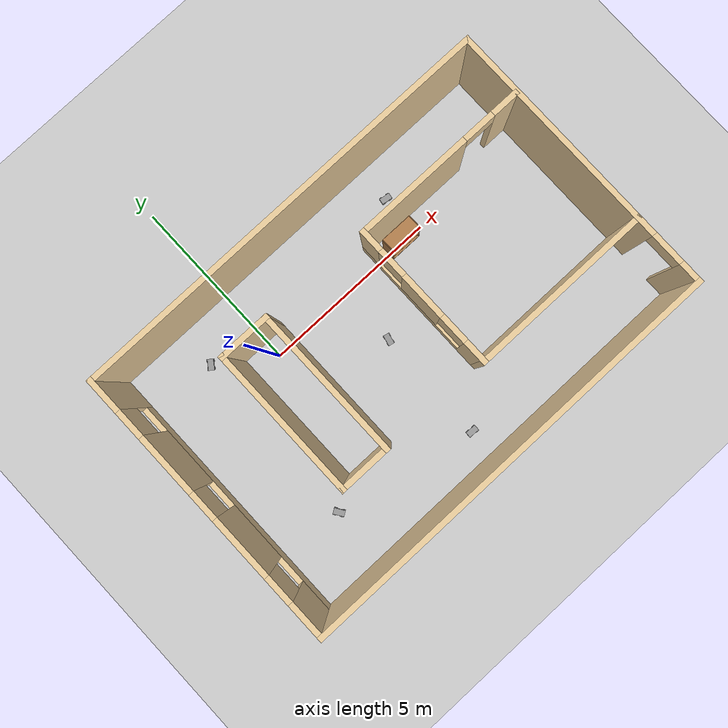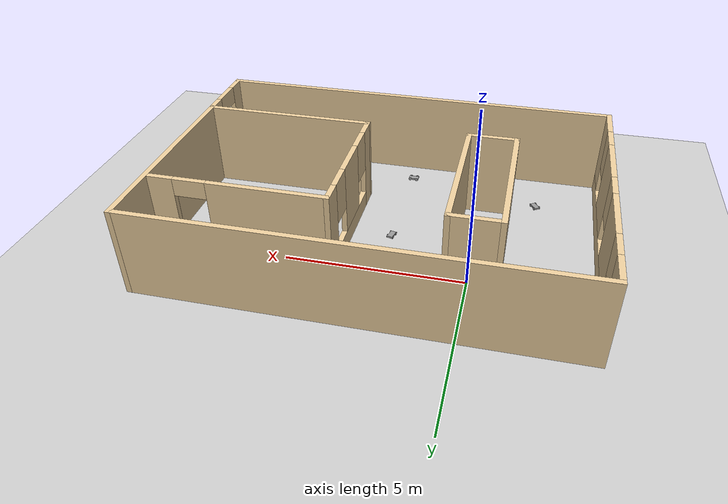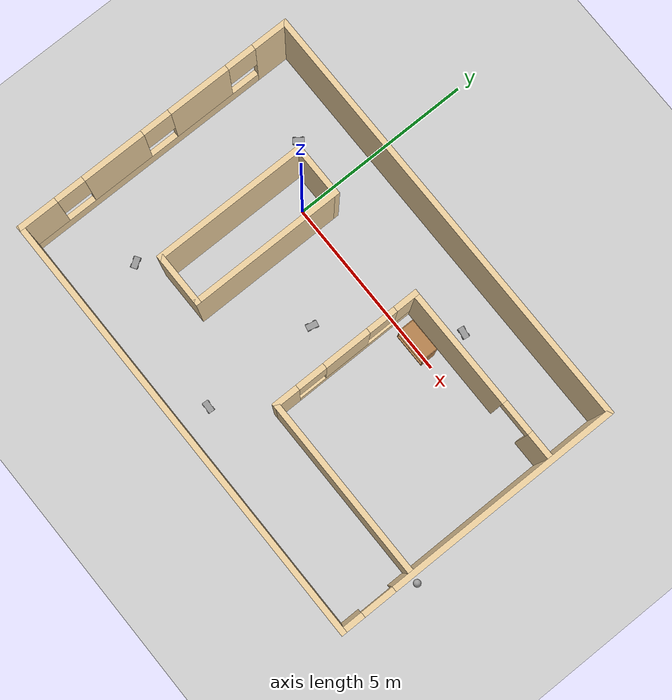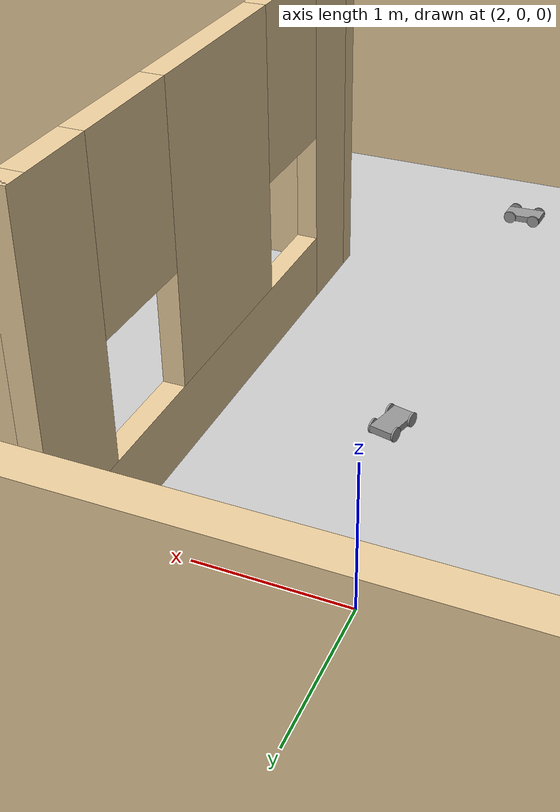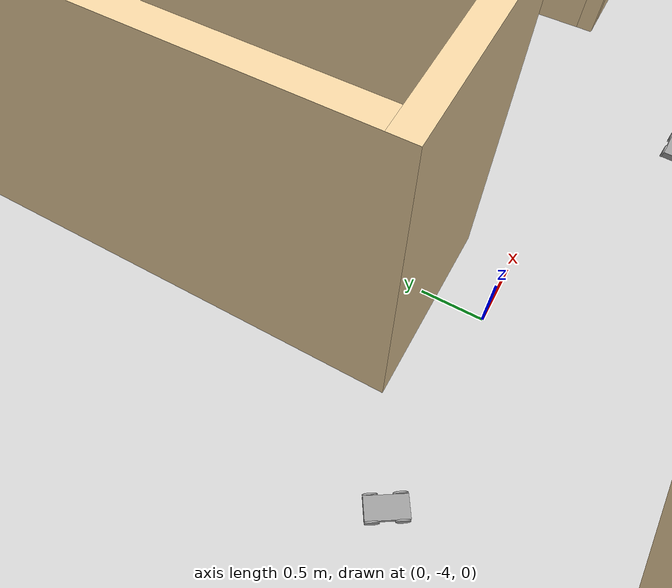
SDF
<sdf version="1.6">
 <world name="default">
  <light name="sun" type="directional">
   <pose>0 0 10 0 -0 0</pose>
   <diffuse>0.8 0.8 0.8 1</diffuse>
   <specular>0.2 0.2 0.2 1</specular>
   <attenuation>
    <range>1000</range>
    <constant>0.9</constant>
    <linear>0.01</linear>
    <quadratic>0.001</quadratic>
   </attenuation>
   <direction>-0.5 0.1 -0.9</direction>
  </light>
  <model name="ground_plane">
   <static>1</static>
   <link name="link">
    <collision name="collision">
     <geometry><plane><normal>0 0 1</normal><size>100 100</size></plane></geometry>
     <surface><friction><ode><mu>100</mu><mu2>50</mu2></ode></friction></surface>
    </collision>
    <visual name="visual">
     <cast_shadows>0</cast_shadows>
     <geometry><plane><normal>0 0 1</normal><size>100 100</size></plane></geometry>
     <material>
      <script><uri>file://media/materials/scripts/gazebo.material</uri><name>Gazebo/Grey</name></script>
     </material>
    </visual>
   </link>
  </model>
  <gravity>0 0 -9.8</gravity>
  <magnetic_field>6e-06 2.3e-05 -4.2e-05</magnetic_field>
  <atmosphere type="adiabatic"/>
  <physics name="default_physics" default="0" type="ode">
   <max_step_size>0.001</max_step_size>
   <real_time_factor>1</real_time_factor>
   <real_time_update_rate>1000</real_time_update_rate>
  </physics>
  <scene><ambient>0.4 0.4 0.4 1</ambient><background>0.7 0.7 0.7 1</background><shadows>1</shadows></scene>
  <spherical_coordinates>
   <surface_model>EARTH_WGS84</surface_model>
   <latitude_deg>0</latitude_deg>
   <longitude_deg>0</longitude_deg>
   <elevation>0</elevation>
   <heading_deg>0</heading_deg>
  </spherical_coordinates>
  <model name="Robosweeper">
   <link name="link_0">
    <pose>-0 0 0 0 0.05 0</pose>
    <inertial>
     <mass>1</mass>
     <inertia>
      <ixx>0.166667</ixx>
      <ixy>0</ixy>
      <ixz>0</ixz>
      <iyy>0.166667</iyy>
      <iyz>0</iyz>
      <izz>0.166667</izz>
     </inertia>
    </inertial>
    <visual name="visual">
     <geometry><box><size>0.3 0.16 0.05</size></box></geometry>
     <material>
      <lighting>1</lighting>
      <script><uri>file://media/materials/scripts/gazebo.material</uri><name>Gazebo/Grey</name></script>
      <ambient>0.3 0.3 0.3 1</ambient>
      <diffuse>0.7 0.7 0.7 1</diffuse>
      <specular>0.01 0.01 0.01 1</specular>
      <emissive>0 0 0 1</emissive>
      <shader type="vertex"><normal_map>__default__</normal_map></shader>
     </material>
    </visual>
    <collision name="collision">
     <geometry><box><size>0.3 0.16 0.05</size></box></geometry>
     <surface>
      <friction>
       <ode><mu>1</mu><mu2>1</mu2><fdir1>0 0 0</fdir1><slip1>0</slip1><slip2>0</slip2></ode>
       <torsional>
        <coefficient>1</coefficient>
        <patch_radius>0</patch_radius>
        <surface_radius>0</surface_radius>
        <use_patch_radius>1</use_patch_radius>
        <ode><slip>0</slip></ode>
       </torsional>
      </friction>
      <bounce><restitution_coefficient>0</restitution_coefficient><threshold>1e+06</threshold></bounce>
      <contact>
       <collide_without_contact>0</collide_without_contact>
       <collide_without_contact_bitmask>1</collide_without_contact_bitmask>
       <collide_bitmask>1</collide_bitmask>
       <ode>
        <soft_cfm>0</soft_cfm>
        <soft_erp>0.2</soft_erp>
        <kp>1e+13</kp>
        <kd>1</kd>
        <max_vel>0.01</max_vel>
        <min_depth>0</min_depth>
       </ode>
       <bullet>
        <split_impulse>1</split_impulse>
        <split_impulse_penetration_threshold>-0.01</split_impulse_penetration_threshold>
        <soft_cfm>0</soft_cfm>
        <soft_erp>0.2</soft_erp>
        <kp>1e+13</kp>
        <kd>1</kd>
       </bullet>
      </contact>
     </surface>
    </collision>
   </link>
   <link name="link_1">
    <pose>-0.1 0.086203 0 1.5707 -0 0</pose>
    <inertial>
     <mass>1</mass>
     <inertia><ixx>0.145833</ixx><ixy>0</ixy><ixz>0</ixz><iyy>0.145833</iyy><iyz>0</iyz><izz>0.125</izz></inertia>
    </inertial>
    <visual name="visual">
     <geometry><cylinder><radius>0.05</radius><length>0.0125</length></cylinder></geometry>
     <material>
      <lighting>1</lighting>
      <script><uri>file://media/materials/scripts/gazebo.material</uri><name>Gazebo/Grey</name></script>
      <ambient>0.3 0.3 0.3 1</ambient>
      <diffuse>0.7 0.7 0.7 1</diffuse>
      <specular>0.01 0.01 0.01 1</specular>
      <emissive>0 0 0 1</emissive>
      <shader type="vertex"><normal_map>__default__</normal_map></shader>
     </material>
    </visual>
    <collision name="collision">
     <geometry><cylinder><radius>0.05</radius><length>0.0125</length></cylinder></geometry>
     <surface>
      <friction>
       <ode><mu>1</mu><mu2>1</mu2><fdir1>0 0 0</fdir1><slip1>0</slip1><slip2>0</slip2></ode>
       <torsional>
        <coefficient>1</coefficient>
        <patch_radius>0</patch_radius>
        <surface_radius>0</surface_radius>
        <use_patch_radius>1</use_patch_radius>
        <ode><slip>0</slip></ode>
       </torsional>
      </friction>
      <bounce><restitution_coefficient>0</restitution_coefficient><threshold>1e+06</threshold></bounce>
      <contact>
       <collide_without_contact>0</collide_without_contact>
       <collide_without_contact_bitmask>1</collide_without_contact_bitmask>
       <collide_bitmask>1</collide_bitmask>
       <ode>
        <soft_cfm>0</soft_cfm>
        <soft_erp>0.2</soft_erp>
        <kp>1e+13</kp>
        <kd>1</kd>
        <max_vel>0.01</max_vel>
        <min_depth>0</min_depth>
       </ode>
       <bullet>
        <split_impulse>1</split_impulse>
        <split_impulse_penetration_threshold>-0.01</split_impulse_penetration_threshold>
        <soft_cfm>0</soft_cfm>
        <soft_erp>0.2</soft_erp>
        <kp>1e+13</kp>
        <kd>1</kd>
       </bullet>
      </contact>
     </surface>
    </collision>
   </link>
   <link name="link_1_clone">
    <pose>0.1 0.086203 0 1.5707 -0 0</pose>
    <inertial>
     <mass>1</mass>
     <inertia><ixx>0.145833</ixx><ixy>0</ixy><ixz>0</ixz><iyy>0.145833</iyy><iyz>0</iyz><izz>0.125</izz></inertia>
    </inertial>
    <visual name="visual">
     <geometry><cylinder><radius>0.05</radius><length>0.0125</length></cylinder></geometry>
     <material>
      <lighting>1</lighting>
      <script><uri>file://media/materials/scripts/gazebo.material</uri><name>Gazebo/Grey</name></script>
      <ambient>0.3 0.3 0.3 1</ambient>
      <diffuse>0.7 0.7 0.7 1</diffuse>
      <specular>0.01 0.01 0.01 1</specular>
      <emissive>0 0 0 1</emissive>
      <shader type="vertex"><normal_map>__default__</normal_map></shader>
     </material>
    </visual>
    <collision name="collision">
     <geometry><cylinder><radius>0.05</radius><length>0.0125</length></cylinder></geometry>
     <surface>
      <friction>
       <ode><mu>1</mu><mu2>1</mu2><fdir1>0 0 0</fdir1><slip1>0</slip1><slip2>0</slip2></ode>
       <torsional>
        <coefficient>1</coefficient>
        <patch_radius>0</patch_radius>
        <surface_radius>0</surface_radius>
        <use_patch_radius>1</use_patch_radius>
        <ode><slip>0</slip></ode>
       </torsional>
      </friction>
      <bounce><restitution_coefficient>0</restitution_coefficient><threshold>1e+06</threshold></bounce>
      <contact>
       <collide_without_contact>0</collide_without_contact>
       <collide_without_contact_bitmask>1</collide_without_contact_bitmask>
       <collide_bitmask>1</collide_bitmask>
       <ode>
        <soft_cfm>0</soft_cfm>
        <soft_erp>0.2</soft_erp>
        <kp>1e+13</kp>
        <kd>1</kd>
        <max_vel>0.01</max_vel>
        <min_depth>0</min_depth>
       </ode>
       <bullet>
        <split_impulse>1</split_impulse>
        <split_impulse_penetration_threshold>-0.01</split_impulse_penetration_threshold>
        <soft_cfm>0</soft_cfm>
        <soft_erp>0.2</soft_erp>
        <kp>1e+13</kp>
        <kd>1</kd>
       </bullet>
      </contact>
     </surface>
    </collision>
   </link>
   <link name="link_1_clone_0">
    <pose>-0.1 -0.086297 0 1.5707 -0 0</pose>
    <inertial>
     <mass>1</mass>
     <inertia><ixx>0.145833</ixx><ixy>0</ixy><ixz>0</ixz><iyy>0.145833</iyy><iyz>0</iyz><izz>0.125</izz></inertia>
    </inertial>
    <visual name="visual">
     <geometry><cylinder><radius>0.05</radius><length>0.0125</length></cylinder></geometry>
     <material>
      <lighting>1</lighting>
      <script><uri>file://media/materials/scripts/gazebo.material</uri><name>Gazebo/Grey</name></script>
      <ambient>0.3 0.3 0.3 1</ambient>
      <diffuse>0.7 0.7 0.7 1</diffuse>
      <specular>0.01 0.01 0.01 1</specular>
      <emissive>0 0 0 1</emissive>
      <shader type="vertex"><normal_map>__default__</normal_map></shader>
     </material>
    </visual>
    <collision name="collision">
     <geometry><cylinder><radius>0.05</radius><length>0.0125</length></cylinder></geometry>
     <surface>
      <friction>
       <ode><mu>1</mu><mu2>1</mu2><fdir1>0 0 0</fdir1><slip1>0</slip1><slip2>0</slip2></ode>
       <torsional>
        <coefficient>1</coefficient>
        <patch_radius>0</patch_radius>
        <surface_radius>0</surface_radius>
        <use_patch_radius>1</use_patch_radius>
        <ode><slip>0</slip></ode>
       </torsional>
      </friction>
      <bounce><restitution_coefficient>0</restitution_coefficient><threshold>1e+06</threshold></bounce>
      <contact>
       <collide_without_contact>0</collide_without_contact>
       <collide_without_contact_bitmask>1</collide_without_contact_bitmask>
       <collide_bitmask>1</collide_bitmask>
       <ode>
        <soft_cfm>0</soft_cfm>
        <soft_erp>0.2</soft_erp>
        <kp>1e+13</kp>
        <kd>1</kd>
        <max_vel>0.01</max_vel>
        <min_depth>0</min_depth>
       </ode>
       <bullet>
        <split_impulse>1</split_impulse>
        <split_impulse_penetration_threshold>-0.01</split_impulse_penetration_threshold>
        <soft_cfm>0</soft_cfm>
        <soft_erp>0.2</soft_erp>
        <kp>1e+13</kp>
        <kd>1</kd>
       </bullet>
      </contact>
     </surface>
    </collision>
   </link>
   <link name="link_1_clone_1">
    <pose>0.1 -0.086297 0 1.5707 -0 0</pose>
    <inertial>
     <mass>1</mass>
     <inertia><ixx>0.145833</ixx><ixy>0</ixy><ixz>0</ixz><iyy>0.145833</iyy><iyz>0</iyz><izz>0.125</izz></inertia>
    </inertial>
    <visual name="visual">
     <geometry><cylinder><radius>0.05</radius><length>0.0125</length></cylinder></geometry>
     <material>
      <lighting>1</lighting>
      <script><uri>file://media/materials/scripts/gazebo.material</uri><name>Gazebo/Grey</name></script>
      <ambient>0.3 0.3 0.3 1</ambient>
      <diffuse>0.7 0.7 0.7 1</diffuse>
      <specular>0.01 0.01 0.01 1</specular>
      <emissive>0 0 0 1</emissive>
      <shader type="vertex"><normal_map>__default__</normal_map></shader>
     </material>
    </visual>
    <collision name="collision">
     <geometry><cylinder><radius>0.05</radius><length>0.0125</length></cylinder></geometry>
     <surface>
      <friction>
       <ode><mu>1</mu><mu2>1</mu2><fdir1>0 0 0</fdir1><slip1>0</slip1><slip2>0</slip2></ode>
       <torsional>
        <coefficient>1</coefficient>
        <patch_radius>0</patch_radius>
        <surface_radius>0</surface_radius>
        <use_patch_radius>1</use_patch_radius>
        <ode><slip>0</slip></ode>
       </torsional>
      </friction>
      <bounce><restitution_coefficient>0</restitution_coefficient><threshold>1e+06</threshold></bounce>
      <contact>
       <collide_without_contact>0</collide_without_contact>
       <collide_without_contact_bitmask>1</collide_without_contact_bitmask>
       <collide_bitmask>1</collide_bitmask>
       <ode>
        <soft_cfm>0</soft_cfm>
        <soft_erp>0.2</soft_erp>
        <kp>1e+13</kp>
        <kd>1</kd>
        <max_vel>0.01</max_vel>
        <min_depth>0</min_depth>
       </ode>
       <bullet>
        <split_impulse>1</split_impulse>
        <split_impulse_penetration_threshold>-0.01</split_impulse_penetration_threshold>
        <soft_cfm>0</soft_cfm>
        <soft_erp>0.2</soft_erp>
        <kp>1e+13</kp>
        <kd>1</kd>
       </bullet>
      </contact>
     </surface>
    </collision>
   </link>
   <joint name="link_0_JOINT_0" type="revolute">
    <parent>link_0</parent>
    <child>link_1</child>
    <axis>
     <xyz>0 0 1</xyz>
     <use_parent_model_frame>0</use_parent_model_frame>
     <limit>
      <lower>-1.79769e+308</lower>
      <upper>1.79769e+308</upper>
      <effort>-1</effort>
      <velocity>-1</velocity>
     </limit>
     <dynamics>
      <spring_reference>0</spring_reference>
      <spring_stiffness>0</spring_stiffness>
      <damping>0</damping>
     </dynamics>
    </axis>
    <physics>
     <ode><limit><cfm>0</cfm><erp>0.2</erp></limit><suspension><cfm>0</cfm><erp>0.2</erp></suspension></ode>
    </physics>
   </joint>
   <joint name="link_0_JOINT_1" type="revolute">
    <parent>link_0</parent>
    <child>link_1_clone</child>
    <axis>
     <xyz>0 0 1</xyz>
     <use_parent_model_frame>0</use_parent_model_frame>
     <limit>
      <lower>-1.79769e+308</lower>
      <upper>1.79769e+308</upper>
      <effort>-1</effort>
      <velocity>-1</velocity>
     </limit>
     <dynamics>
      <spring_reference>0</spring_reference>
      <spring_stiffness>0</spring_stiffness>
      <damping>0</damping>
     </dynamics>
    </axis>
    <physics>
     <ode><limit><cfm>0</cfm><erp>0.2</erp></limit><suspension><cfm>0</cfm><erp>0.2</erp></suspension></ode>
    </physics>
   </joint>
   <joint name="link_0_JOINT_2" type="revolute">
    <parent>link_0</parent>
    <child>link_1_clone_0</child>
    <axis>
     <xyz>0 0 1</xyz>
     <use_parent_model_frame>0</use_parent_model_frame>
     <limit>
      <lower>-1.79769e+308</lower>
      <upper>1.79769e+308</upper>
      <effort>-1</effort>
      <velocity>-1</velocity>
     </limit>
     <dynamics>
      <spring_reference>0</spring_reference>
      <spring_stiffness>0</spring_stiffness>
      <damping>0</damping>
     </dynamics>
    </axis>
    <physics>
     <ode><limit><cfm>0</cfm><erp>0.2</erp></limit><suspension><cfm>0</cfm><erp>0.2</erp></suspension></ode>
    </physics>
   </joint>
   <joint name="link_0_JOINT_3" type="revolute">
    <parent>link_0</parent>
    <child>link_1_clone_1</child>
    <axis>
     <xyz>0 0 1</xyz>
     <use_parent_model_frame>0</use_parent_model_frame>
     <limit>
      <lower>-1.79769e+308</lower>
      <upper>1.79769e+308</upper>
      <effort>-1</effort>
      <velocity>-1</velocity>
     </limit>
     <dynamics>
      <spring_reference>0</spring_reference>
      <spring_stiffness>0</spring_stiffness>
      <damping>0</damping>
     </dynamics>
    </axis>
    <physics>
     <ode><limit><cfm>0</cfm><erp>0.2</erp></limit><suspension><cfm>0</cfm><erp>0.2</erp></suspension></ode>
    </physics>
   </joint>
   <static>0</static>
   <pose>2.33666 -4.82024 0.050001 -3e-06 3e-06 -0.049888</pose>
  </model>
  <model name="Robosweeper_0">
   <link name="link_0">
    <pose>-0 0 0 0 0.05 0</pose>
    <inertial>
     <mass>1</mass>
     <inertia>
      <ixx>0.166667</ixx>
      <ixy>0</ixy>
      <ixz>0</ixz>
      <iyy>0.166667</iyy>
      <iyz>0</iyz>
      <izz>0.166667</izz>
     </inertia>
    </inertial>
    <visual name="visual">
     <geometry><box><size>0.3 0.16 0.05</size></box></geometry>
     <material>
      <lighting>1</lighting>
      <script><uri>file://media/materials/scripts/gazebo.material</uri><name>Gazebo/Grey</name></script>
      <ambient>0.3 0.3 0.3 1</ambient>
      <diffuse>0.7 0.7 0.7 1</diffuse>
      <specular>0.01 0.01 0.01 1</specular>
      <emissive>0 0 0 1</emissive>
      <shader type="vertex"><normal_map>__default__</normal_map></shader>
     </material>
    </visual>
    <collision name="collision">
     <geometry><box><size>0.3 0.16 0.05</size></box></geometry>
     <surface>
      <friction>
       <ode><mu>1</mu><mu2>1</mu2><fdir1>0 0 0</fdir1><slip1>0</slip1><slip2>0</slip2></ode>
       <torsional>
        <coefficient>1</coefficient>
        <patch_radius>0</patch_radius>
        <surface_radius>0</surface_radius>
        <use_patch_radius>1</use_patch_radius>
        <ode><slip>0</slip></ode>
       </torsional>
      </friction>
      <bounce><restitution_coefficient>0</restitution_coefficient><threshold>1e+06</threshold></bounce>
      <contact>
       <collide_without_contact>0</collide_without_contact>
       <collide_without_contact_bitmask>1</collide_without_contact_bitmask>
       <collide_bitmask>1</collide_bitmask>
       <ode>
        <soft_cfm>0</soft_cfm>
        <soft_erp>0.2</soft_erp>
        <kp>1e+13</kp>
        <kd>1</kd>
        <max_vel>0.01</max_vel>
        <min_depth>0</min_depth>
       </ode>
       <bullet>
        <split_impulse>1</split_impulse>
        <split_impulse_penetration_threshold>-0.01</split_impulse_penetration_threshold>
        <soft_cfm>0</soft_cfm>
        <soft_erp>0.2</soft_erp>
        <kp>1e+13</kp>
        <kd>1</kd>
       </bullet>
      </contact>
     </surface>
    </collision>
   </link>
   <link name="link_1">
    <pose>-0.1 0.086203 0 1.5707 -0 0</pose>
    <inertial>
     <mass>1</mass>
     <inertia><ixx>0.145833</ixx><ixy>0</ixy><ixz>0</ixz><iyy>0.145833</iyy><iyz>0</iyz><izz>0.125</izz></inertia>
    </inertial>
    <visual name="visual">
     <geometry><cylinder><radius>0.05</radius><length>0.0125</length></cylinder></geometry>
     <material>
      <lighting>1</lighting>
      <script><uri>file://media/materials/scripts/gazebo.material</uri><name>Gazebo/Grey</name></script>
      <ambient>0.3 0.3 0.3 1</ambient>
      <diffuse>0.7 0.7 0.7 1</diffuse>
      <specular>0.01 0.01 0.01 1</specular>
      <emissive>0 0 0 1</emissive>
      <shader type="vertex"><normal_map>__default__</normal_map></shader>
     </material>
    </visual>
    <collision name="collision">
     <geometry><cylinder><radius>0.05</radius><length>0.0125</length></cylinder></geometry>
     <surface>
      <friction>
       <ode><mu>1</mu><mu2>1</mu2><fdir1>0 0 0</fdir1><slip1>0</slip1><slip2>0</slip2></ode>
       <torsional>
        <coefficient>1</coefficient>
        <patch_radius>0</patch_radius>
        <surface_radius>0</surface_radius>
        <use_patch_radius>1</use_patch_radius>
        <ode><slip>0</slip></ode>
       </torsional>
      </friction>
      <bounce><restitution_coefficient>0</restitution_coefficient><threshold>1e+06</threshold></bounce>
      <contact>
       <collide_without_contact>0</collide_without_contact>
       <collide_without_contact_bitmask>1</collide_without_contact_bitmask>
       <collide_bitmask>1</collide_bitmask>
       <ode>
        <soft_cfm>0</soft_cfm>
        <soft_erp>0.2</soft_erp>
        <kp>1e+13</kp>
        <kd>1</kd>
        <max_vel>0.01</max_vel>
        <min_depth>0</min_depth>
       </ode>
       <bullet>
        <split_impulse>1</split_impulse>
        <split_impulse_penetration_threshold>-0.01</split_impulse_penetration_threshold>
        <soft_cfm>0</soft_cfm>
        <soft_erp>0.2</soft_erp>
        <kp>1e+13</kp>
        <kd>1</kd>
       </bullet>
      </contact>
     </surface>
    </collision>
   </link>
   <link name="link_1_clone">
    <pose>0.1 0.086203 0 1.5707 -0 0</pose>
    <inertial>
     <mass>1</mass>
     <inertia><ixx>0.145833</ixx><ixy>0</ixy><ixz>0</ixz><iyy>0.145833</iyy><iyz>0</iyz><izz>0.125</izz></inertia>
    </inertial>
    <visual name="visual">
     <geometry><cylinder><radius>0.05</radius><length>0.0125</length></cylinder></geometry>
     <material>
      <lighting>1</lighting>
      <script><uri>file://media/materials/scripts/gazebo.material</uri><name>Gazebo/Grey</name></script>
      <ambient>0.3 0.3 0.3 1</ambient>
      <diffuse>0.7 0.7 0.7 1</diffuse>
      <specular>0.01 0.01 0.01 1</specular>
      <emissive>0 0 0 1</emissive>
      <shader type="vertex"><normal_map>__default__</normal_map></shader>
     </material>
    </visual>
    <collision name="collision">
     <geometry><cylinder><radius>0.05</radius><length>0.0125</length></cylinder></geometry>
     <surface>
      <friction>
       <ode><mu>1</mu><mu2>1</mu2><fdir1>0 0 0</fdir1><slip1>0</slip1><slip2>0</slip2></ode>
       <torsional>
        <coefficient>1</coefficient>
        <patch_radius>0</patch_radius>
        <surface_radius>0</surface_radius>
        <use_patch_radius>1</use_patch_radius>
        <ode><slip>0</slip></ode>
       </torsional>
      </friction>
      <bounce><restitution_coefficient>0</restitution_coefficient><threshold>1e+06</threshold></bounce>
      <contact>
       <collide_without_contact>0</collide_without_contact>
       <collide_without_contact_bitmask>1</collide_without_contact_bitmask>
       <collide_bitmask>1</collide_bitmask>
       <ode>
        <soft_cfm>0</soft_cfm>
        <soft_erp>0.2</soft_erp>
        <kp>1e+13</kp>
        <kd>1</kd>
        <max_vel>0.01</max_vel>
        <min_depth>0</min_depth>
       </ode>
       <bullet>
        <split_impulse>1</split_impulse>
        <split_impulse_penetration_threshold>-0.01</split_impulse_penetration_threshold>
        <soft_cfm>0</soft_cfm>
        <soft_erp>0.2</soft_erp>
        <kp>1e+13</kp>
        <kd>1</kd>
       </bullet>
      </contact>
     </surface>
    </collision>
   </link>
   <link name="link_1_clone_0">
    <pose>-0.1 -0.086297 0 1.5707 -0 0</pose>
    <inertial>
     <mass>1</mass>
     <inertia><ixx>0.145833</ixx><ixy>0</ixy><ixz>0</ixz><iyy>0.145833</iyy><iyz>0</iyz><izz>0.125</izz></inertia>
    </inertial>
    <visual name="visual">
     <geometry><cylinder><radius>0.05</radius><length>0.0125</length></cylinder></geometry>
     <material>
      <lighting>1</lighting>
      <script><uri>file://media/materials/scripts/gazebo.material</uri><name>Gazebo/Grey</name></script>
      <ambient>0.3 0.3 0.3 1</ambient>
      <diffuse>0.7 0.7 0.7 1</diffuse>
      <specular>0.01 0.01 0.01 1</specular>
      <emissive>0 0 0 1</emissive>
      <shader type="vertex"><normal_map>__default__</normal_map></shader>
     </material>
    </visual>
    <collision name="collision">
     <geometry><cylinder><radius>0.05</radius><length>0.0125</length></cylinder></geometry>
     <surface>
      <friction>
       <ode><mu>1</mu><mu2>1</mu2><fdir1>0 0 0</fdir1><slip1>0</slip1><slip2>0</slip2></ode>
       <torsional>
        <coefficient>1</coefficient>
        <patch_radius>0</patch_radius>
        <surface_radius>0</surface_radius>
        <use_patch_radius>1</use_patch_radius>
        <ode><slip>0</slip></ode>
       </torsional>
      </friction>
      <bounce><restitution_coefficient>0</restitution_coefficient><threshold>1e+06</threshold></bounce>
      <contact>
       <collide_without_contact>0</collide_without_contact>
       <collide_without_contact_bitmask>1</collide_without_contact_bitmask>
       <collide_bitmask>1</collide_bitmask>
       <ode>
        <soft_cfm>0</soft_cfm>
        <soft_erp>0.2</soft_erp>
        <kp>1e+13</kp>
        <kd>1</kd>
        <max_vel>0.01</max_vel>
        <min_depth>0</min_depth>
       </ode>
       <bullet>
        <split_impulse>1</split_impulse>
        <split_impulse_penetration_threshold>-0.01</split_impulse_penetration_threshold>
        <soft_cfm>0</soft_cfm>
        <soft_erp>0.2</soft_erp>
        <kp>1e+13</kp>
        <kd>1</kd>
       </bullet>
      </contact>
     </surface>
    </collision>
   </link>
   <link name="link_1_clone_1">
    <pose>0.1 -0.086297 0 1.5707 -0 0</pose>
    <inertial>
     <mass>1</mass>
     <inertia><ixx>0.145833</ixx><ixy>0</ixy><ixz>0</ixz><iyy>0.145833</iyy><iyz>0</iyz><izz>0.125</izz></inertia>
    </inertial>
    <visual name="visual">
     <geometry><cylinder><radius>0.05</radius><length>0.0125</length></cylinder></geometry>
     <material>
      <lighting>1</lighting>
      <script><uri>file://media/materials/scripts/gazebo.material</uri><name>Gazebo/Grey</name></script>
      <ambient>0.3 0.3 0.3 1</ambient>
      <diffuse>0.7 0.7 0.7 1</diffuse>
      <specular>0.01 0.01 0.01 1</specular>
      <emissive>0 0 0 1</emissive>
      <shader type="vertex"><normal_map>__default__</normal_map></shader>
     </material>
    </visual>
    <collision name="collision">
     <geometry><cylinder><radius>0.05</radius><length>0.0125</length></cylinder></geometry>
     <surface>
      <friction>
       <ode><mu>1</mu><mu2>1</mu2><fdir1>0 0 0</fdir1><slip1>0</slip1><slip2>0</slip2></ode>
       <torsional>
        <coefficient>1</coefficient>
        <patch_radius>0</patch_radius>
        <surface_radius>0</surface_radius>
        <use_patch_radius>1</use_patch_radius>
        <ode><slip>0</slip></ode>
       </torsional>
      </friction>
      <bounce><restitution_coefficient>0</restitution_coefficient><threshold>1e+06</threshold></bounce>
      <contact>
       <collide_without_contact>0</collide_without_contact>
       <collide_without_contact_bitmask>1</collide_without_contact_bitmask>
       <collide_bitmask>1</collide_bitmask>
       <ode>
        <soft_cfm>0</soft_cfm>
        <soft_erp>0.2</soft_erp>
        <kp>1e+13</kp>
        <kd>1</kd>
        <max_vel>0.01</max_vel>
        <min_depth>0</min_depth>
       </ode>
       <bullet>
        <split_impulse>1</split_impulse>
        <split_impulse_penetration_threshold>-0.01</split_impulse_penetration_threshold>
        <soft_cfm>0</soft_cfm>
        <soft_erp>0.2</soft_erp>
        <kp>1e+13</kp>
        <kd>1</kd>
       </bullet>
      </contact>
     </surface>
    </collision>
   </link>
   <joint name="link_0_JOINT_0" type="revolute">
    <parent>link_0</parent>
    <child>link_1</child>
    <axis>
     <xyz>0 0 1</xyz>
     <use_parent_model_frame>0</use_parent_model_frame>
     <limit>
      <lower>-1.79769e+308</lower>
      <upper>1.79769e+308</upper>
      <effort>-1</effort>
      <velocity>-1</velocity>
     </limit>
     <dynamics>
      <spring_reference>0</spring_reference>
      <spring_stiffness>0</spring_stiffness>
      <damping>0</damping>
     </dynamics>
    </axis>
    <physics>
     <ode><limit><cfm>0</cfm><erp>0.2</erp></limit><suspension><cfm>0</cfm><erp>0.2</erp></suspension></ode>
    </physics>
   </joint>
   <joint name="link_0_JOINT_1" type="revolute">
    <parent>link_0</parent>
    <child>link_1_clone</child>
    <axis>
     <xyz>0 0 1</xyz>
     <use_parent_model_frame>0</use_parent_model_frame>
     <limit>
      <lower>-1.79769e+308</lower>
      <upper>1.79769e+308</upper>
      <effort>-1</effort>
      <velocity>-1</velocity>
     </limit>
     <dynamics>
      <spring_reference>0</spring_reference>
      <spring_stiffness>0</spring_stiffness>
      <damping>0</damping>
     </dynamics>
    </axis>
    <physics>
     <ode><limit><cfm>0</cfm><erp>0.2</erp></limit><suspension><cfm>0</cfm><erp>0.2</erp></suspension></ode>
    </physics>
   </joint>
   <joint name="link_0_JOINT_2" type="revolute">
    <parent>link_0</parent>
    <child>link_1_clone_0</child>
    <axis>
     <xyz>0 0 1</xyz>
     <use_parent_model_frame>0</use_parent_model_frame>
     <limit>
      <lower>-1.79769e+308</lower>
      <upper>1.79769e+308</upper>
      <effort>-1</effort>
      <velocity>-1</velocity>
     </limit>
     <dynamics>
      <spring_reference>0</spring_reference>
      <spring_stiffness>0</spring_stiffness>
      <damping>0</damping>
     </dynamics>
    </axis>
    <physics>
     <ode><limit><cfm>0</cfm><erp>0.2</erp></limit><suspension><cfm>0</cfm><erp>0.2</erp></suspension></ode>
    </physics>
   </joint>
   <joint name="link_0_JOINT_3" type="revolute">
    <parent>link_0</parent>
    <child>link_1_clone_1</child>
    <axis>
     <xyz>0 0 1</xyz>
     <use_parent_model_frame>0</use_parent_model_frame>
     <limit>
      <lower>-1.79769e+308</lower>
      <upper>1.79769e+308</upper>
      <effort>-1</effort>
      <velocity>-1</velocity>
     </limit>
     <dynamics>
      <spring_reference>0</spring_reference>
      <spring_stiffness>0</spring_stiffness>
      <damping>0</damping>
     </dynamics>
    </axis>
    <physics>
     <ode><limit><cfm>0</cfm><erp>0.2</erp></limit><suspension><cfm>0</cfm><erp>0.2</erp></suspension></ode>
    </physics>
   </joint>
   <static>0</static>
   <pose>-1.57609 -4.0019 0.049999 -5e-06 1.5e-05 -1.0052</pose>
  </model>
  <model name="Shop_Floor">
   <pose>2.53883 -1.71757 0 0 -0 0</pose>
   <link name="Wall_0">
    <pose>-5.925 0 0 0 0 -1.5708</pose>
    <visual name="Wall_0_Visual_0">
     <pose>-3.48792 0 1.25 0 -0 0</pose>
     <geometry><box><size>1.02416 0.15 2.5</size></box></geometry>
     <material>
      <script><uri>file://media/materials/scripts/gazebo.material</uri><name>Gazebo/Grey</name></script>
      <ambient>0.921569 0.807843 0.615686 1</ambient>
     </material>
     <meta><layer>0</layer></meta>
    </visual>
    <collision name="Wall_0_Collision_0">
     <geometry><box><size>1.02416 0.15 2.5</size></box></geometry>
     <pose>-3.48792 0 1.25 0 -0 0</pose>
    </collision>
    <visual name="Wall_0_Visual_1">
     <pose>0.512079 0 0.25 0 -0 0</pose>
     <geometry><box><size>6.97584 0.15 0.5</size></box></geometry>
     <material>
      <script><uri>file://media/materials/scripts/gazebo.material</uri><name>Gazebo/Grey</name></script>
      <ambient>0.921569 0.807843 0.615686 1</ambient>
     </material>
     <meta><layer>0</layer></meta>
    </visual>
    <collision name="Wall_0_Collision_1">
     <geometry><box><size>6.97584 0.15 0.5</size></box></geometry>
     <pose>0.512079 0 0.25 0 -0 0</pose>
    </collision>
    <visual name="Wall_0_Visual_2">
     <pose>-1.31522 0 1.5 0 -0 0</pose>
     <geometry><box><size>1.72124 0.15 2</size></box></geometry>
     <material>
      <script><uri>file://media/materials/scripts/gazebo.material</uri><name>Gazebo/Grey</name></script>
      <ambient>0.921569 0.807843 0.615686 1</ambient>
     </material>
     <meta><layer>0</layer></meta>
    </visual>
    <collision name="Wall_0_Collision_2">
     <geometry><box><size>1.72124 0.15 2</size></box></geometry>
     <pose>-1.31522 0 1.5 0 -0 0</pose>
    </collision>
    <visual name="Wall_0_Visual_3">
     <pose>1.22048 0 1.5 0 -0 0</pose>
     <geometry><box><size>1.75017 0.15 2</size></box></geometry>
     <material>
      <script><uri>file://media/materials/scripts/gazebo.material</uri><name>Gazebo/Grey</name></script>
      <ambient>0.921569 0.807843 0.615686 1</ambient>
     </material>
     <meta><layer>0</layer></meta>
    </visual>
    <collision name="Wall_0_Collision_3">
     <geometry><box><size>1.75017 0.15 2</size></box></geometry>
     <pose>1.22048 0 1.5 0 -0 0</pose>
    </collision>
    <visual name="Wall_0_Visual_4">
     <pose>3.44778 0 1.5 0 -0 0</pose>
     <geometry><box><size>1.10444 0.15 2</size></box></geometry>
     <material>
      <script><uri>file://media/materials/scripts/gazebo.material</uri><name>Gazebo/Grey</name></script>
      <ambient>0.921569 0.807843 0.615686 1</ambient>
     </material>
     <meta><layer>0</layer></meta>
    </visual>
    <collision name="Wall_0_Collision_4">
     <geometry><box><size>1.10444 0.15 2</size></box></geometry>
     <pose>3.44778 0 1.5 0 -0 0</pose>
    </collision>
    <visual name="Wall_0_Visual_5">
     <pose>-2.57584 0 1.9 0 -0 0</pose>
     <geometry><box><size>0.8 0.15 1.2</size></box></geometry>
     <material>
      <script><uri>file://media/materials/scripts/gazebo.material</uri><name>Gazebo/Grey</name></script>
      <ambient>0.921569 0.807843 0.615686 1</ambient>
     </material>
     <meta><layer>0</layer></meta>
    </visual>
    <collision name="Wall_0_Collision_5">
     <geometry><box><size>0.8 0.15 1.2</size></box></geometry>
     <pose>-2.57584 0 1.9 0 -0 0</pose>
    </collision>
    <visual name="Wall_0_Visual_6">
     <pose>-0.054606 0 1.9 0 -0 0</pose>
     <geometry><box><size>0.8 0.15 1.2</size></box></geometry>
     <material>
      <script><uri>file://media/materials/scripts/gazebo.material</uri><name>Gazebo/Grey</name></script>
      <ambient>0.921569 0.807843 0.615686 1</ambient>
     </material>
     <meta><layer>0</layer></meta>
    </visual>
    <collision name="Wall_0_Collision_6">
     <geometry><box><size>0.8 0.15 1.2</size></box></geometry>
     <pose>-0.054606 0 1.9 0 -0 0</pose>
    </collision>
    <visual name="Wall_0_Visual_7">
     <pose>2.49556 0 1.9 0 -0 0</pose>
     <geometry><box><size>0.8 0.15 1.2</size></box></geometry>
     <material>
      <script><uri>file://media/materials/scripts/gazebo.material</uri><name>Gazebo/Grey</name></script>
      <ambient>0.921569 0.807843 0.615686 1</ambient>
     </material>
     <meta><layer>0</layer></meta>
    </visual>
    <collision name="Wall_0_Collision_7">
     <geometry><box><size>0.8 0.15 1.2</size></box></geometry>
     <pose>2.49556 0 1.9 0 -0 0</pose>
    </collision>
   </link>
   <link name="Wall_1">
    <collision name="Wall_1_Collision">
     <geometry><box><size>12 0.15 2.5</size></box></geometry>
     <pose>0 0 1.25 0 -0 0</pose>
    </collision>
    <visual name="Wall_1_Visual">
     <pose>0 0 1.25 0 -0 0</pose>
     <geometry><box><size>12 0.15 2.5</size></box></geometry>
     <material>
      <script><uri>file://media/materials/scripts/gazebo.material</uri><name>Gazebo/Grey</name></script>
      <ambient>0.921569 0.807843 0.615686 1</ambient>
     </material>
     <meta><layer>0</layer></meta>
    </visual>
    <pose>0 -3.925 0 0 -0 0</pose>
   </link>
   <link name="Wall_2">
    <pose>5.925 0 0 0 -0 1.5708</pose>
    <visual name="Wall_2_Visual_0">
     <pose>-3.66386 0 1.25 0 -0 0</pose>
     <geometry><box><size>0.672281 0.15 2.5</size></box></geometry>
     <material>
      <script><uri>file://media/materials/scripts/gazebo.material</uri><name>Gazebo/Grey</name></script>
      <ambient>0.921569 0.807843 0.615686 1</ambient>
     </material>
     <meta><layer>0</layer></meta>
    </visual>
    <collision name="Wall_2_Collision_0">
     <geometry><box><size>0.672281 0.15 2.5</size></box></geometry>
     <pose>-3.66386 0 1.25 0 -0 0</pose>
    </collision>
    <visual name="Wall_2_Visual_1">
     <pose>0.786141 0 1.25 0 -0 0</pose>
     <geometry><box><size>6.42772 0.15 2.5</size></box></geometry>
     <material>
      <script><uri>file://media/materials/scripts/gazebo.material</uri><name>Gazebo/Grey</name></script>
      <ambient>0.921569 0.807843 0.615686 1</ambient>
     </material>
     <meta><layer>0</layer></meta>
    </visual>
    <collision name="Wall_2_Collision_1">
     <geometry><box><size>6.42772 0.15 2.5</size></box></geometry>
     <pose>0.786141 0 1.25 0 -0 0</pose>
    </collision>
    <visual name="Wall_2_Visual_2">
     <pose>-2.87772 0 2.25 0 -0 0</pose>
     <geometry><box><size>0.9 0.15 0.5</size></box></geometry>
     <material>
      <script><uri>file://media/materials/scripts/gazebo.material</uri><name>Gazebo/Grey</name></script>
      <ambient>0.921569 0.807843 0.615686 1</ambient>
     </material>
     <meta><layer>0</layer></meta>
    </visual>
    <collision name="Wall_2_Collision_2">
     <geometry><box><size>0.9 0.15 0.5</size></box></geometry>
     <pose>-2.87772 0 2.25 0 -0 0</pose>
    </collision>
   </link>
   <link name="Wall_20">
    <collision name="Wall_20_Collision">
     <geometry><box><size>4.25 0.15 2.5</size></box></geometry>
     <pose>0 0 1.25 0 -0 0</pose>
    </collision>
    <visual name="Wall_20_Visual">
     <pose>0 0 1.25 0 -0 0</pose>
     <geometry><box><size>4.25 0.15 2.5</size></box></geometry>
     <material>
      <script><uri>file://media/materials/scripts/gazebo.material</uri><name>Gazebo/Grey</name></script>
      <ambient>0.921569 0.807843 0.615686 1</ambient>
     </material>
     <meta><layer>0</layer></meta>
    </visual>
    <pose>-1.99427 0.226904 0 0 -0 1.5708</pose>
   </link>
   <link name="Wall_21">
    <collision name="Wall_21_Collision">
     <geometry><box><size>1.5 0.15 2.5</size></box></geometry>
     <pose>0 0 1.25 0 -0 0</pose>
    </collision>
    <visual name="Wall_21_Visual">
     <pose>0 0 1.25 0 -0 0</pose>
     <geometry><box><size>1.5 0.15 2.5</size></box></geometry>
     <material>
      <script><uri>file://media/materials/scripts/gazebo.material</uri><name>Gazebo/Grey</name></script>
      <ambient>0.921569 0.807843 0.615686 1</ambient>
     </material>
     <meta><layer>0</layer></meta>
    </visual>
    <pose>-2.66927 2.2769 0 0 -0 3.14159</pose>
   </link>
   <link name="Wall_22">
    <collision name="Wall_22_Collision">
     <geometry><box><size>4.25 0.15 2.5</size></box></geometry>
     <pose>0 0 1.25 0 -0 0</pose>
    </collision>
    <visual name="Wall_22_Visual">
     <pose>0 0 1.25 0 -0 0</pose>
     <geometry><box><size>4.25 0.15 2.5</size></box></geometry>
     <material>
      <script><uri>file://media/materials/scripts/gazebo.material</uri><name>Gazebo/Grey</name></script>
      <ambient>0.921569 0.807843 0.615686 1</ambient>
     </material>
     <meta><layer>0</layer></meta>
    </visual>
    <pose>-3.34427 0.226904 0 0 0 -1.5708</pose>
   </link>
   <link name="Wall_23">
    <collision name="Wall_23_Collision">
     <geometry><box><size>1.5 0.15 2.5</size></box></geometry>
     <pose>0 0 1.25 0 -0 0</pose>
    </collision>
    <visual name="Wall_23_Visual">
     <pose>0 0 1.25 0 -0 0</pose>
     <geometry><box><size>1.5 0.15 2.5</size></box></geometry>
     <material>
      <script><uri>file://media/materials/scripts/gazebo.material</uri><name>Gazebo/Grey</name></script>
      <ambient>0.921569 0.807843 0.615686 1</ambient>
     </material>
     <meta><layer>0</layer></meta>
    </visual>
    <pose>-2.66927 -1.8231 0 0 -0 0</pose>
   </link>
   <link name="Wall_25">
    <collision name="Wall_25_Collision">
     <geometry><box><size>5.04563 0.15 2.5</size></box></geometry>
     <pose>0 0 1.25 0 -0 0</pose>
    </collision>
    <visual name="Wall_25_Visual">
     <pose>0 0 1.25 0 -0 0</pose>
     <geometry><box><size>5.04563 0.15 2.5</size></box></geometry>
     <material>
      <script><uri>file://media/materials/scripts/gazebo.material</uri><name>Gazebo/Grey</name></script>
      <ambient>0.921569 0.807843 0.615686 1</ambient>
     </material>
     <meta><layer>0</layer></meta>
    </visual>
    <pose>3.45851 -1.89064 0 0 -0 3.14159</pose>
   </link>
   <link name="Wall_28">
    <pose>1.0107 0.159355 0 0 -0 1.5708</pose>
    <visual name="Wall_28_Visual_0">
     <pose>-1.77536 0 1.25 0 -0 0</pose>
     <geometry><box><size>0.699283 0.15 2.5</size></box></geometry>
     <material>
      <script><uri>file://media/materials/scripts/gazebo.material</uri><name>Gazebo/Grey</name></script>
      <ambient>0.921569 0.807843 0.615686 1</ambient>
     </material>
     <meta><layer>0</layer></meta>
    </visual>
    <collision name="Wall_28_Collision_0">
     <geometry><box><size>0.699283 0.15 2.5</size></box></geometry>
     <pose>-1.77536 0 1.25 0 -0 0</pose>
    </collision>
    <visual name="Wall_28_Visual_1">
     <pose>0.349641 0 0.25 0 -0 0</pose>
     <geometry><box><size>3.55072 0.15 0.5</size></box></geometry>
     <material>
      <script><uri>file://media/materials/scripts/gazebo.material</uri><name>Gazebo/Grey</name></script>
      <ambient>0.921569 0.807843 0.615686 1</ambient>
     </material>
     <meta><layer>0</layer></meta>
    </visual>
    <collision name="Wall_28_Collision_1">
     <geometry><box><size>3.55072 0.15 0.5</size></box></geometry>
     <pose>0.349641 0 0.25 0 -0 0</pose>
    </collision>
    <visual name="Wall_28_Visual_2">
     <pose>0.020189 0 1.5 0 -0 0</pose>
     <geometry><box><size>1.29181 0.15 2</size></box></geometry>
     <material>
      <script><uri>file://media/materials/scripts/gazebo.material</uri><name>Gazebo/Grey</name></script>
      <ambient>0.921569 0.807843 0.615686 1</ambient>
     </material>
     <meta><layer>0</layer></meta>
    </visual>
    <collision name="Wall_28_Collision_2">
     <geometry><box><size>1.29181 0.15 2</size></box></geometry>
     <pose>0.020189 0 1.5 0 -0 0</pose>
    </collision>
    <visual name="Wall_28_Visual_3">
     <pose>1.79555 0 1.5 0 -0 0</pose>
     <geometry><box><size>0.658906 0.15 2</size></box></geometry>
     <material>
      <script><uri>file://media/materials/scripts/gazebo.material</uri><name>Gazebo/Grey</name></script>
      <ambient>0.921569 0.807843 0.615686 1</ambient>
     </material>
     <meta><layer>0</layer></meta>
    </visual>
    <collision name="Wall_28_Collision_3">
     <geometry><box><size>0.658906 0.15 2</size></box></geometry>
     <pose>1.79555 0 1.5 0 -0 0</pose>
    </collision>
    <visual name="Wall_28_Visual_4">
     <pose>-1.02572 0 1.9 0 -0 0</pose>
     <geometry><box><size>0.8 0.15 1.2</size></box></geometry>
     <material>
      <script><uri>file://media/materials/scripts/gazebo.material</uri><name>Gazebo/Grey</name></script>
      <ambient>0.921569 0.807843 0.615686 1</ambient>
     </material>
     <meta><layer>0</layer></meta>
    </visual>
    <collision name="Wall_28_Collision_4">
     <geometry><box><size>0.8 0.15 1.2</size></box></geometry>
     <pose>-1.02572 0 1.9 0 -0 0</pose>
    </collision>
    <visual name="Wall_28_Visual_5">
     <pose>1.06609 0 1.9 0 -0 0</pose>
     <geometry><box><size>0.8 0.15 1.2</size></box></geometry>
     <material>
      <script><uri>file://media/materials/scripts/gazebo.material</uri><name>Gazebo/Grey</name></script>
      <ambient>0.921569 0.807843 0.615686 1</ambient>
     </material>
     <meta><layer>0</layer></meta>
    </visual>
    <collision name="Wall_28_Collision_5">
     <geometry><box><size>0.8 0.15 1.2</size></box></geometry>
     <pose>1.06609 0 1.9 0 -0 0</pose>
    </collision>
   </link>
   <link name="Wall_29">
    <pose>3.4357 2.20935 0 0 -0 0</pose>
    <visual name="Wall_29_Visual_0">
     <pose>-0.847857 0 1.25 0 -0 0</pose>
     <geometry><box><size>3.30429 0.15 2.5</size></box></geometry>
     <material>
      <script><uri>file://media/materials/scripts/gazebo.material</uri><name>Gazebo/Grey</name></script>
      <ambient>0.921569 0.807843 0.615686 1</ambient>
     </material>
     <meta><layer>0</layer></meta>
    </visual>
    <collision name="Wall_29_Collision_0">
     <geometry><box><size>3.30429 0.15 2.5</size></box></geometry>
     <pose>-0.847857 0 1.25 0 -0 0</pose>
    </collision>
    <visual name="Wall_29_Visual_1">
     <pose>2.10214 0 1.25 0 -0 0</pose>
     <geometry><box><size>0.795714 0.15 2.5</size></box></geometry>
     <material>
      <script><uri>file://media/materials/scripts/gazebo.material</uri><name>Gazebo/Grey</name></script>
      <ambient>0.921569 0.807843 0.615686 1</ambient>
     </material>
     <meta><layer>0</layer></meta>
    </visual>
    <collision name="Wall_29_Collision_1">
     <geometry><box><size>0.795714 0.15 2.5</size></box></geometry>
     <pose>2.10214 0 1.25 0 -0 0</pose>
    </collision>
    <visual name="Wall_29_Visual_2">
     <pose>1.25429 0 2.25 0 -0 0</pose>
     <geometry><box><size>0.9 0.15 0.5</size></box></geometry>
     <material>
      <script><uri>file://media/materials/scripts/gazebo.material</uri><name>Gazebo/Grey</name></script>
      <ambient>0.921569 0.807843 0.615686 1</ambient>
     </material>
     <meta><layer>0</layer></meta>
    </visual>
    <collision name="Wall_29_Collision_2">
     <geometry><box><size>0.9 0.15 0.5</size></box></geometry>
     <pose>1.25429 0 2.25 0 -0 0</pose>
    </collision>
   </link>
   <link name="Wall_3">
    <collision name="Wall_3_Collision">
     <geometry><box><size>12 0.15 2.5</size></box></geometry>
     <pose>0 0 1.25 0 -0 0</pose>
    </collision>
    <visual name="Wall_3_Visual">
     <pose>0 0 1.25 0 -0 0</pose>
     <geometry><box><size>12 0.15 2.5</size></box></geometry>
     <material>
      <script><uri>file://media/materials/scripts/gazebo.material</uri><name>Gazebo/Grey</name></script>
      <ambient>0.921569 0.807843 0.615686 1</ambient>
     </material>
     <meta><layer>0</layer></meta>
    </visual>
    <pose>0 3.925 0 0 -0 3.14159</pose>
   </link>
   <static>1</static>
  </model>
  <model name="Robosweeper_clone">
   <link name="link_0">
    <pose>-0 0 0 0 0.05 0</pose>
    <inertial>
     <mass>1</mass>
     <inertia>
      <ixx>0.166667</ixx>
      <ixy>0</ixy>
      <ixz>0</ixz>
      <iyy>0.166667</iyy>
      <iyz>0</iyz>
      <izz>0.166667</izz>
     </inertia>
    </inertial>
    <visual name="visual">
     <geometry><box><size>0.3 0.16 0.05</size></box></geometry>
     <material>
      <lighting>1</lighting>
      <script><uri>file://media/materials/scripts/gazebo.material</uri><name>Gazebo/Grey</name></script>
      <ambient>0.3 0.3 0.3 1</ambient>
      <diffuse>0.7 0.7 0.7 1</diffuse>
      <specular>0.01 0.01 0.01 1</specular>
      <emissive>0 0 0 1</emissive>
      <shader type="vertex"><normal_map>__default__</normal_map></shader>
     </material>
    </visual>
    <collision name="collision">
     <geometry><box><size>0.3 0.16 0.05</size></box></geometry>
     <surface>
      <friction>
       <ode><mu>1</mu><mu2>1</mu2><fdir1>0 0 0</fdir1><slip1>0</slip1><slip2>0</slip2></ode>
       <torsional>
        <coefficient>1</coefficient>
        <patch_radius>0</patch_radius>
        <surface_radius>0</surface_radius>
        <use_patch_radius>1</use_patch_radius>
        <ode><slip>0</slip></ode>
       </torsional>
      </friction>
      <bounce><restitution_coefficient>0</restitution_coefficient><threshold>1e+06</threshold></bounce>
      <contact>
       <collide_without_contact>0</collide_without_contact>
       <collide_without_contact_bitmask>1</collide_without_contact_bitmask>
       <collide_bitmask>1</collide_bitmask>
       <ode>
        <soft_cfm>0</soft_cfm>
        <soft_erp>0.2</soft_erp>
        <kp>1e+13</kp>
        <kd>1</kd>
        <max_vel>0.01</max_vel>
        <min_depth>0</min_depth>
       </ode>
       <bullet>
        <split_impulse>1</split_impulse>
        <split_impulse_penetration_threshold>-0.01</split_impulse_penetration_threshold>
        <soft_cfm>0</soft_cfm>
        <soft_erp>0.2</soft_erp>
        <kp>1e+13</kp>
        <kd>1</kd>
       </bullet>
      </contact>
     </surface>
    </collision>
   </link>
   <link name="link_1">
    <pose>-0.1 0.086203 0 1.5707 -0 0</pose>
    <inertial>
     <mass>1</mass>
     <inertia><ixx>0.145833</ixx><ixy>0</ixy><ixz>0</ixz><iyy>0.145833</iyy><iyz>0</iyz><izz>0.125</izz></inertia>
    </inertial>
    <visual name="visual">
     <geometry><cylinder><radius>0.05</radius><length>0.0125</length></cylinder></geometry>
     <material>
      <lighting>1</lighting>
      <script><uri>file://media/materials/scripts/gazebo.material</uri><name>Gazebo/Grey</name></script>
      <ambient>0.3 0.3 0.3 1</ambient>
      <diffuse>0.7 0.7 0.7 1</diffuse>
      <specular>0.01 0.01 0.01 1</specular>
      <emissive>0 0 0 1</emissive>
      <shader type="vertex"><normal_map>__default__</normal_map></shader>
     </material>
    </visual>
    <collision name="collision">
     <geometry><cylinder><radius>0.05</radius><length>0.0125</length></cylinder></geometry>
     <surface>
      <friction>
       <ode><mu>1</mu><mu2>1</mu2><fdir1>0 0 0</fdir1><slip1>0</slip1><slip2>0</slip2></ode>
       <torsional>
        <coefficient>1</coefficient>
        <patch_radius>0</patch_radius>
        <surface_radius>0</surface_radius>
        <use_patch_radius>1</use_patch_radius>
        <ode><slip>0</slip></ode>
       </torsional>
      </friction>
      <bounce><restitution_coefficient>0</restitution_coefficient><threshold>1e+06</threshold></bounce>
      <contact>
       <collide_without_contact>0</collide_without_contact>
       <collide_without_contact_bitmask>1</collide_without_contact_bitmask>
       <collide_bitmask>1</collide_bitmask>
       <ode>
        <soft_cfm>0</soft_cfm>
        <soft_erp>0.2</soft_erp>
        <kp>1e+13</kp>
        <kd>1</kd>
        <max_vel>0.01</max_vel>
        <min_depth>0</min_depth>
       </ode>
       <bullet>
        <split_impulse>1</split_impulse>
        <split_impulse_penetration_threshold>-0.01</split_impulse_penetration_threshold>
        <soft_cfm>0</soft_cfm>
        <soft_erp>0.2</soft_erp>
        <kp>1e+13</kp>
        <kd>1</kd>
       </bullet>
      </contact>
     </surface>
    </collision>
   </link>
   <link name="link_1_clone">
    <pose>0.1 0.086203 0 1.5707 -0 0</pose>
    <inertial>
     <mass>1</mass>
     <inertia><ixx>0.145833</ixx><ixy>0</ixy><ixz>0</ixz><iyy>0.145833</iyy><iyz>0</iyz><izz>0.125</izz></inertia>
    </inertial>
    <visual name="visual">
     <geometry><cylinder><radius>0.05</radius><length>0.0125</length></cylinder></geometry>
     <material>
      <lighting>1</lighting>
      <script><uri>file://media/materials/scripts/gazebo.material</uri><name>Gazebo/Grey</name></script>
      <ambient>0.3 0.3 0.3 1</ambient>
      <diffuse>0.7 0.7 0.7 1</diffuse>
      <specular>0.01 0.01 0.01 1</specular>
      <emissive>0 0 0 1</emissive>
      <shader type="vertex"><normal_map>__default__</normal_map></shader>
     </material>
    </visual>
    <collision name="collision">
     <geometry><cylinder><radius>0.05</radius><length>0.0125</length></cylinder></geometry>
     <surface>
      <friction>
       <ode><mu>1</mu><mu2>1</mu2><fdir1>0 0 0</fdir1><slip1>0</slip1><slip2>0</slip2></ode>
       <torsional>
        <coefficient>1</coefficient>
        <patch_radius>0</patch_radius>
        <surface_radius>0</surface_radius>
        <use_patch_radius>1</use_patch_radius>
        <ode><slip>0</slip></ode>
       </torsional>
      </friction>
      <bounce><restitution_coefficient>0</restitution_coefficient><threshold>1e+06</threshold></bounce>
      <contact>
       <collide_without_contact>0</collide_without_contact>
       <collide_without_contact_bitmask>1</collide_without_contact_bitmask>
       <collide_bitmask>1</collide_bitmask>
       <ode>
        <soft_cfm>0</soft_cfm>
        <soft_erp>0.2</soft_erp>
        <kp>1e+13</kp>
        <kd>1</kd>
        <max_vel>0.01</max_vel>
        <min_depth>0</min_depth>
       </ode>
       <bullet>
        <split_impulse>1</split_impulse>
        <split_impulse_penetration_threshold>-0.01</split_impulse_penetration_threshold>
        <soft_cfm>0</soft_cfm>
        <soft_erp>0.2</soft_erp>
        <kp>1e+13</kp>
        <kd>1</kd>
       </bullet>
      </contact>
     </surface>
    </collision>
   </link>
   <link name="link_1_clone_0">
    <pose>-0.1 -0.086297 0 1.5707 -0 0</pose>
    <inertial>
     <mass>1</mass>
     <inertia><ixx>0.145833</ixx><ixy>0</ixy><ixz>0</ixz><iyy>0.145833</iyy><iyz>0</iyz><izz>0.125</izz></inertia>
    </inertial>
    <visual name="visual">
     <geometry><cylinder><radius>0.05</radius><length>0.0125</length></cylinder></geometry>
     <material>
      <lighting>1</lighting>
      <script><uri>file://media/materials/scripts/gazebo.material</uri><name>Gazebo/Grey</name></script>
      <ambient>0.3 0.3 0.3 1</ambient>
      <diffuse>0.7 0.7 0.7 1</diffuse>
      <specular>0.01 0.01 0.01 1</specular>
      <emissive>0 0 0 1</emissive>
      <shader type="vertex"><normal_map>__default__</normal_map></shader>
     </material>
    </visual>
    <collision name="collision">
     <geometry><cylinder><radius>0.05</radius><length>0.0125</length></cylinder></geometry>
     <surface>
      <friction>
       <ode><mu>1</mu><mu2>1</mu2><fdir1>0 0 0</fdir1><slip1>0</slip1><slip2>0</slip2></ode>
       <torsional>
        <coefficient>1</coefficient>
        <patch_radius>0</patch_radius>
        <surface_radius>0</surface_radius>
        <use_patch_radius>1</use_patch_radius>
        <ode><slip>0</slip></ode>
       </torsional>
      </friction>
      <bounce><restitution_coefficient>0</restitution_coefficient><threshold>1e+06</threshold></bounce>
      <contact>
       <collide_without_contact>0</collide_without_contact>
       <collide_without_contact_bitmask>1</collide_without_contact_bitmask>
       <collide_bitmask>1</collide_bitmask>
       <ode>
        <soft_cfm>0</soft_cfm>
        <soft_erp>0.2</soft_erp>
        <kp>1e+13</kp>
        <kd>1</kd>
        <max_vel>0.01</max_vel>
        <min_depth>0</min_depth>
       </ode>
       <bullet>
        <split_impulse>1</split_impulse>
        <split_impulse_penetration_threshold>-0.01</split_impulse_penetration_threshold>
        <soft_cfm>0</soft_cfm>
        <soft_erp>0.2</soft_erp>
        <kp>1e+13</kp>
        <kd>1</kd>
       </bullet>
      </contact>
     </surface>
    </collision>
   </link>
   <link name="link_1_clone_1">
    <pose>0.1 -0.086297 0 1.5707 -0 0</pose>
    <inertial>
     <mass>1</mass>
     <inertia><ixx>0.145833</ixx><ixy>0</ixy><ixz>0</ixz><iyy>0.145833</iyy><iyz>0</iyz><izz>0.125</izz></inertia>
    </inertial>
    <visual name="visual">
     <geometry><cylinder><radius>0.05</radius><length>0.0125</length></cylinder></geometry>
     <material>
      <lighting>1</lighting>
      <script><uri>file://media/materials/scripts/gazebo.material</uri><name>Gazebo/Grey</name></script>
      <ambient>0.3 0.3 0.3 1</ambient>
      <diffuse>0.7 0.7 0.7 1</diffuse>
      <specular>0.01 0.01 0.01 1</specular>
      <emissive>0 0 0 1</emissive>
      <shader type="vertex"><normal_map>__default__</normal_map></shader>
     </material>
    </visual>
    <collision name="collision">
     <geometry><cylinder><radius>0.05</radius><length>0.0125</length></cylinder></geometry>
     <surface>
      <friction>
       <ode><mu>1</mu><mu2>1</mu2><fdir1>0 0 0</fdir1><slip1>0</slip1><slip2>0</slip2></ode>
       <torsional>
        <coefficient>1</coefficient>
        <patch_radius>0</patch_radius>
        <surface_radius>0</surface_radius>
        <use_patch_radius>1</use_patch_radius>
        <ode><slip>0</slip></ode>
       </torsional>
      </friction>
      <bounce><restitution_coefficient>0</restitution_coefficient><threshold>1e+06</threshold></bounce>
      <contact>
       <collide_without_contact>0</collide_without_contact>
       <collide_without_contact_bitmask>1</collide_without_contact_bitmask>
       <collide_bitmask>1</collide_bitmask>
       <ode>
        <soft_cfm>0</soft_cfm>
        <soft_erp>0.2</soft_erp>
        <kp>1e+13</kp>
        <kd>1</kd>
        <max_vel>0.01</max_vel>
        <min_depth>0</min_depth>
       </ode>
       <bullet>
        <split_impulse>1</split_impulse>
        <split_impulse_penetration_threshold>-0.01</split_impulse_penetration_threshold>
        <soft_cfm>0</soft_cfm>
        <soft_erp>0.2</soft_erp>
        <kp>1e+13</kp>
        <kd>1</kd>
       </bullet>
      </contact>
     </surface>
    </collision>
   </link>
   <joint name="link_0_JOINT_0" type="revolute">
    <parent>link_0</parent>
    <child>link_1</child>
    <axis>
     <xyz>0 0 1</xyz>
     <use_parent_model_frame>0</use_parent_model_frame>
     <limit>
      <lower>-1.79769e+308</lower>
      <upper>1.79769e+308</upper>
      <effort>-1</effort>
      <velocity>-1</velocity>
     </limit>
     <dynamics>
      <spring_reference>0</spring_reference>
      <spring_stiffness>0</spring_stiffness>
      <damping>0</damping>
     </dynamics>
    </axis>
    <physics>
     <ode><limit><cfm>0</cfm><erp>0.2</erp></limit><suspension><cfm>0</cfm><erp>0.2</erp></suspension></ode>
    </physics>
   </joint>
   <joint name="link_0_JOINT_1" type="revolute">
    <parent>link_0</parent>
    <child>link_1_clone</child>
    <axis>
     <xyz>0 0 1</xyz>
     <use_parent_model_frame>0</use_parent_model_frame>
     <limit>
      <lower>-1.79769e+308</lower>
      <upper>1.79769e+308</upper>
      <effort>-1</effort>
      <velocity>-1</velocity>
     </limit>
     <dynamics>
      <spring_reference>0</spring_reference>
      <spring_stiffness>0</spring_stiffness>
      <damping>0</damping>
     </dynamics>
    </axis>
    <physics>
     <ode><limit><cfm>0</cfm><erp>0.2</erp></limit><suspension><cfm>0</cfm><erp>0.2</erp></suspension></ode>
    </physics>
   </joint>
   <joint name="link_0_JOINT_2" type="revolute">
    <parent>link_0</parent>
    <child>link_1_clone_0</child>
    <axis>
     <xyz>0 0 1</xyz>
     <use_parent_model_frame>0</use_parent_model_frame>
     <limit>
      <lower>-1.79769e+308</lower>
      <upper>1.79769e+308</upper>
      <effort>-1</effort>
      <velocity>-1</velocity>
     </limit>
     <dynamics>
      <spring_reference>0</spring_reference>
      <spring_stiffness>0</spring_stiffness>
      <damping>0</damping>
     </dynamics>
    </axis>
    <physics>
     <ode><limit><cfm>0</cfm><erp>0.2</erp></limit><suspension><cfm>0</cfm><erp>0.2</erp></suspension></ode>
    </physics>
   </joint>
   <joint name="link_0_JOINT_3" type="revolute">
    <parent>link_0</parent>
    <child>link_1_clone_1</child>
    <axis>
     <xyz>0 0 1</xyz>
     <use_parent_model_frame>0</use_parent_model_frame>
     <limit>
      <lower>-1.79769e+308</lower>
      <upper>1.79769e+308</upper>
      <effort>-1</effort>
      <velocity>-1</velocity>
     </limit>
     <dynamics>
      <spring_reference>0</spring_reference>
      <spring_stiffness>0</spring_stiffness>
      <damping>0</damping>
     </dynamics>
    </axis>
    <physics>
     <ode><limit><cfm>0</cfm><erp>0.2</erp></limit><suspension><cfm>0</cfm><erp>0.2</erp></suspension></ode>
    </physics>
   </joint>
   <static>0</static>
   <pose>2.36867 -1.61146 0.050002 -3e-06 -8e-06 -1.79502</pose>
  </model>
  <model name="Robosweeper_0_clone">
   <link name="link_0">
    <pose>-0 0 0 0 0.05 0</pose>
    <inertial>
     <mass>1</mass>
     <inertia>
      <ixx>0.166667</ixx>
      <ixy>0</ixy>
      <ixz>0</ixz>
      <iyy>0.166667</iyy>
      <iyz>0</iyz>
      <izz>0.166667</izz>
     </inertia>
    </inertial>
    <visual name="visual">
     <geometry><box><size>0.3 0.16 0.05</size></box></geometry>
     <material>
      <lighting>1</lighting>
      <script><uri>file://media/materials/scripts/gazebo.material</uri><name>Gazebo/Grey</name></script>
      <ambient>0.3 0.3 0.3 1</ambient>
      <diffuse>0.7 0.7 0.7 1</diffuse>
      <specular>0.01 0.01 0.01 1</specular>
      <emissive>0 0 0 1</emissive>
      <shader type="vertex"><normal_map>__default__</normal_map></shader>
     </material>
    </visual>
    <collision name="collision">
     <geometry><box><size>0.3 0.16 0.05</size></box></geometry>
     <surface>
      <friction>
       <ode><mu>1</mu><mu2>1</mu2><fdir1>0 0 0</fdir1><slip1>0</slip1><slip2>0</slip2></ode>
       <torsional>
        <coefficient>1</coefficient>
        <patch_radius>0</patch_radius>
        <surface_radius>0</surface_radius>
        <use_patch_radius>1</use_patch_radius>
        <ode><slip>0</slip></ode>
       </torsional>
      </friction>
      <bounce><restitution_coefficient>0</restitution_coefficient><threshold>1e+06</threshold></bounce>
      <contact>
       <collide_without_contact>0</collide_without_contact>
       <collide_without_contact_bitmask>1</collide_without_contact_bitmask>
       <collide_bitmask>1</collide_bitmask>
       <ode>
        <soft_cfm>0</soft_cfm>
        <soft_erp>0.2</soft_erp>
        <kp>1e+13</kp>
        <kd>1</kd>
        <max_vel>0.01</max_vel>
        <min_depth>0</min_depth>
       </ode>
       <bullet>
        <split_impulse>1</split_impulse>
        <split_impulse_penetration_threshold>-0.01</split_impulse_penetration_threshold>
        <soft_cfm>0</soft_cfm>
        <soft_erp>0.2</soft_erp>
        <kp>1e+13</kp>
        <kd>1</kd>
       </bullet>
      </contact>
     </surface>
    </collision>
   </link>
   <link name="link_1">
    <pose>-0.1 0.086203 0 1.5707 -0 0</pose>
    <inertial>
     <mass>1</mass>
     <inertia><ixx>0.145833</ixx><ixy>0</ixy><ixz>0</ixz><iyy>0.145833</iyy><iyz>0</iyz><izz>0.125</izz></inertia>
    </inertial>
    <visual name="visual">
     <geometry><cylinder><radius>0.05</radius><length>0.0125</length></cylinder></geometry>
     <material>
      <lighting>1</lighting>
      <script><uri>file://media/materials/scripts/gazebo.material</uri><name>Gazebo/Grey</name></script>
      <ambient>0.3 0.3 0.3 1</ambient>
      <diffuse>0.7 0.7 0.7 1</diffuse>
      <specular>0.01 0.01 0.01 1</specular>
      <emissive>0 0 0 1</emissive>
      <shader type="vertex"><normal_map>__default__</normal_map></shader>
     </material>
    </visual>
    <collision name="collision">
     <geometry><cylinder><radius>0.05</radius><length>0.0125</length></cylinder></geometry>
     <surface>
      <friction>
       <ode><mu>1</mu><mu2>1</mu2><fdir1>0 0 0</fdir1><slip1>0</slip1><slip2>0</slip2></ode>
       <torsional>
        <coefficient>1</coefficient>
        <patch_radius>0</patch_radius>
        <surface_radius>0</surface_radius>
        <use_patch_radius>1</use_patch_radius>
        <ode><slip>0</slip></ode>
       </torsional>
      </friction>
      <bounce><restitution_coefficient>0</restitution_coefficient><threshold>1e+06</threshold></bounce>
      <contact>
       <collide_without_contact>0</collide_without_contact>
       <collide_without_contact_bitmask>1</collide_without_contact_bitmask>
       <collide_bitmask>1</collide_bitmask>
       <ode>
        <soft_cfm>0</soft_cfm>
        <soft_erp>0.2</soft_erp>
        <kp>1e+13</kp>
        <kd>1</kd>
        <max_vel>0.01</max_vel>
        <min_depth>0</min_depth>
       </ode>
       <bullet>
        <split_impulse>1</split_impulse>
        <split_impulse_penetration_threshold>-0.01</split_impulse_penetration_threshold>
        <soft_cfm>0</soft_cfm>
        <soft_erp>0.2</soft_erp>
        <kp>1e+13</kp>
        <kd>1</kd>
       </bullet>
      </contact>
     </surface>
    </collision>
   </link>
   <link name="link_1_clone">
    <pose>0.1 0.086203 0 1.5707 -0 0</pose>
    <inertial>
     <mass>1</mass>
     <inertia><ixx>0.145833</ixx><ixy>0</ixy><ixz>0</ixz><iyy>0.145833</iyy><iyz>0</iyz><izz>0.125</izz></inertia>
    </inertial>
    <visual name="visual">
     <geometry><cylinder><radius>0.05</radius><length>0.0125</length></cylinder></geometry>
     <material>
      <lighting>1</lighting>
      <script><uri>file://media/materials/scripts/gazebo.material</uri><name>Gazebo/Grey</name></script>
      <ambient>0.3 0.3 0.3 1</ambient>
      <diffuse>0.7 0.7 0.7 1</diffuse>
      <specular>0.01 0.01 0.01 1</specular>
      <emissive>0 0 0 1</emissive>
      <shader type="vertex"><normal_map>__default__</normal_map></shader>
     </material>
    </visual>
    <collision name="collision">
     <geometry><cylinder><radius>0.05</radius><length>0.0125</length></cylinder></geometry>
     <surface>
      <friction>
       <ode><mu>1</mu><mu2>1</mu2><fdir1>0 0 0</fdir1><slip1>0</slip1><slip2>0</slip2></ode>
       <torsional>
        <coefficient>1</coefficient>
        <patch_radius>0</patch_radius>
        <surface_radius>0</surface_radius>
        <use_patch_radius>1</use_patch_radius>
        <ode><slip>0</slip></ode>
       </torsional>
      </friction>
      <bounce><restitution_coefficient>0</restitution_coefficient><threshold>1e+06</threshold></bounce>
      <contact>
       <collide_without_contact>0</collide_without_contact>
       <collide_without_contact_bitmask>1</collide_without_contact_bitmask>
       <collide_bitmask>1</collide_bitmask>
       <ode>
        <soft_cfm>0</soft_cfm>
        <soft_erp>0.2</soft_erp>
        <kp>1e+13</kp>
        <kd>1</kd>
        <max_vel>0.01</max_vel>
        <min_depth>0</min_depth>
       </ode>
       <bullet>
        <split_impulse>1</split_impulse>
        <split_impulse_penetration_threshold>-0.01</split_impulse_penetration_threshold>
        <soft_cfm>0</soft_cfm>
        <soft_erp>0.2</soft_erp>
        <kp>1e+13</kp>
        <kd>1</kd>
       </bullet>
      </contact>
     </surface>
    </collision>
   </link>
   <link name="link_1_clone_0">
    <pose>-0.1 -0.086297 0 1.5707 -0 0</pose>
    <inertial>
     <mass>1</mass>
     <inertia><ixx>0.145833</ixx><ixy>0</ixy><ixz>0</ixz><iyy>0.145833</iyy><iyz>0</iyz><izz>0.125</izz></inertia>
    </inertial>
    <visual name="visual">
     <geometry><cylinder><radius>0.05</radius><length>0.0125</length></cylinder></geometry>
     <material>
      <lighting>1</lighting>
      <script><uri>file://media/materials/scripts/gazebo.material</uri><name>Gazebo/Grey</name></script>
      <ambient>0.3 0.3 0.3 1</ambient>
      <diffuse>0.7 0.7 0.7 1</diffuse>
      <specular>0.01 0.01 0.01 1</specular>
      <emissive>0 0 0 1</emissive>
      <shader type="vertex"><normal_map>__default__</normal_map></shader>
     </material>
    </visual>
    <collision name="collision">
     <geometry><cylinder><radius>0.05</radius><length>0.0125</length></cylinder></geometry>
     <surface>
      <friction>
       <ode><mu>1</mu><mu2>1</mu2><fdir1>0 0 0</fdir1><slip1>0</slip1><slip2>0</slip2></ode>
       <torsional>
        <coefficient>1</coefficient>
        <patch_radius>0</patch_radius>
        <surface_radius>0</surface_radius>
        <use_patch_radius>1</use_patch_radius>
        <ode><slip>0</slip></ode>
       </torsional>
      </friction>
      <bounce><restitution_coefficient>0</restitution_coefficient><threshold>1e+06</threshold></bounce>
      <contact>
       <collide_without_contact>0</collide_without_contact>
       <collide_without_contact_bitmask>1</collide_without_contact_bitmask>
       <collide_bitmask>1</collide_bitmask>
       <ode>
        <soft_cfm>0</soft_cfm>
        <soft_erp>0.2</soft_erp>
        <kp>1e+13</kp>
        <kd>1</kd>
        <max_vel>0.01</max_vel>
        <min_depth>0</min_depth>
       </ode>
       <bullet>
        <split_impulse>1</split_impulse>
        <split_impulse_penetration_threshold>-0.01</split_impulse_penetration_threshold>
        <soft_cfm>0</soft_cfm>
        <soft_erp>0.2</soft_erp>
        <kp>1e+13</kp>
        <kd>1</kd>
       </bullet>
      </contact>
     </surface>
    </collision>
   </link>
   <link name="link_1_clone_1">
    <pose>0.1 -0.086297 0 1.5707 -0 0</pose>
    <inertial>
     <mass>1</mass>
     <inertia><ixx>0.145833</ixx><ixy>0</ixy><ixz>0</ixz><iyy>0.145833</iyy><iyz>0</iyz><izz>0.125</izz></inertia>
    </inertial>
    <visual name="visual">
     <geometry><cylinder><radius>0.05</radius><length>0.0125</length></cylinder></geometry>
     <material>
      <lighting>1</lighting>
      <script><uri>file://media/materials/scripts/gazebo.material</uri><name>Gazebo/Grey</name></script>
      <ambient>0.3 0.3 0.3 1</ambient>
      <diffuse>0.7 0.7 0.7 1</diffuse>
      <specular>0.01 0.01 0.01 1</specular>
      <emissive>0 0 0 1</emissive>
      <shader type="vertex"><normal_map>__default__</normal_map></shader>
     </material>
    </visual>
    <collision name="collision">
     <geometry><cylinder><radius>0.05</radius><length>0.0125</length></cylinder></geometry>
     <surface>
      <friction>
       <ode><mu>1</mu><mu2>1</mu2><fdir1>0 0 0</fdir1><slip1>0</slip1><slip2>0</slip2></ode>
       <torsional>
        <coefficient>1</coefficient>
        <patch_radius>0</patch_radius>
        <surface_radius>0</surface_radius>
        <use_patch_radius>1</use_patch_radius>
        <ode><slip>0</slip></ode>
       </torsional>
      </friction>
      <bounce><restitution_coefficient>0</restitution_coefficient><threshold>1e+06</threshold></bounce>
      <contact>
       <collide_without_contact>0</collide_without_contact>
       <collide_without_contact_bitmask>1</collide_without_contact_bitmask>
       <collide_bitmask>1</collide_bitmask>
       <ode>
        <soft_cfm>0</soft_cfm>
        <soft_erp>0.2</soft_erp>
        <kp>1e+13</kp>
        <kd>1</kd>
        <max_vel>0.01</max_vel>
        <min_depth>0</min_depth>
       </ode>
       <bullet>
        <split_impulse>1</split_impulse>
        <split_impulse_penetration_threshold>-0.01</split_impulse_penetration_threshold>
        <soft_cfm>0</soft_cfm>
        <soft_erp>0.2</soft_erp>
        <kp>1e+13</kp>
        <kd>1</kd>
       </bullet>
      </contact>
     </surface>
    </collision>
   </link>
   <joint name="link_0_JOINT_0" type="revolute">
    <parent>link_0</parent>
    <child>link_1</child>
    <axis>
     <xyz>0 0 1</xyz>
     <use_parent_model_frame>0</use_parent_model_frame>
     <limit>
      <lower>-1.79769e+308</lower>
      <upper>1.79769e+308</upper>
      <effort>-1</effort>
      <velocity>-1</velocity>
     </limit>
     <dynamics>
      <spring_reference>0</spring_reference>
      <spring_stiffness>0</spring_stiffness>
      <damping>0</damping>
     </dynamics>
    </axis>
    <physics>
     <ode><limit><cfm>0</cfm><erp>0.2</erp></limit><suspension><cfm>0</cfm><erp>0.2</erp></suspension></ode>
    </physics>
   </joint>
   <joint name="link_0_JOINT_1" type="revolute">
    <parent>link_0</parent>
    <child>link_1_clone</child>
    <axis>
     <xyz>0 0 1</xyz>
     <use_parent_model_frame>0</use_parent_model_frame>
     <limit>
      <lower>-1.79769e+308</lower>
      <upper>1.79769e+308</upper>
      <effort>-1</effort>
      <velocity>-1</velocity>
     </limit>
     <dynamics>
      <spring_reference>0</spring_reference>
      <spring_stiffness>0</spring_stiffness>
      <damping>0</damping>
     </dynamics>
    </axis>
    <physics>
     <ode><limit><cfm>0</cfm><erp>0.2</erp></limit><suspension><cfm>0</cfm><erp>0.2</erp></suspension></ode>
    </physics>
   </joint>
   <joint name="link_0_JOINT_2" type="revolute">
    <parent>link_0</parent>
    <child>link_1_clone_0</child>
    <axis>
     <xyz>0 0 1</xyz>
     <use_parent_model_frame>0</use_parent_model_frame>
     <limit>
      <lower>-1.79769e+308</lower>
      <upper>1.79769e+308</upper>
      <effort>-1</effort>
      <velocity>-1</velocity>
     </limit>
     <dynamics>
      <spring_reference>0</spring_reference>
      <spring_stiffness>0</spring_stiffness>
      <damping>0</damping>
     </dynamics>
    </axis>
    <physics>
     <ode><limit><cfm>0</cfm><erp>0.2</erp></limit><suspension><cfm>0</cfm><erp>0.2</erp></suspension></ode>
    </physics>
   </joint>
   <joint name="link_0_JOINT_3" type="revolute">
    <parent>link_0</parent>
    <child>link_1_clone_1</child>
    <axis>
     <xyz>0 0 1</xyz>
     <use_parent_model_frame>0</use_parent_model_frame>
     <limit>
      <lower>-1.79769e+308</lower>
      <upper>1.79769e+308</upper>
      <effort>-1</effort>
      <velocity>-1</velocity>
     </limit>
     <dynamics>
      <spring_reference>0</spring_reference>
      <spring_stiffness>0</spring_stiffness>
      <damping>0</damping>
     </dynamics>
    </axis>
    <physics>
     <ode><limit><cfm>0</cfm><erp>0.2</erp></limit><suspension><cfm>0</cfm><erp>0.2</erp></suspension></ode>
    </physics>
   </joint>
   <static>0</static>
   <pose>-1.46099 1.04589 0.05 -1e-06 0 -2.19803</pose>
  </model>
  <model name="Robosweeper_0_clone_0">
   <link name="link_0">
    <pose>-0 0 0 0 0.05 0</pose>
    <inertial>
     <mass>1</mass>
     <inertia>
      <ixx>0.166667</ixx>
      <ixy>0</ixy>
      <ixz>0</ixz>
      <iyy>0.166667</iyy>
      <iyz>0</iyz>
      <izz>0.166667</izz>
     </inertia>
    </inertial>
    <visual name="visual">
     <geometry><box><size>0.3 0.16 0.05</size></box></geometry>
     <material>
      <lighting>1</lighting>
      <script><uri>file://media/materials/scripts/gazebo.material</uri><name>Gazebo/Grey</name></script>
      <ambient>0.3 0.3 0.3 1</ambient>
      <diffuse>0.7 0.7 0.7 1</diffuse>
      <specular>0.01 0.01 0.01 1</specular>
      <emissive>0 0 0 1</emissive>
      <shader type="vertex"><normal_map>__default__</normal_map></shader>
     </material>
    </visual>
    <collision name="collision">
     <geometry><box><size>0.3 0.16 0.05</size></box></geometry>
     <surface>
      <friction>
       <ode><mu>1</mu><mu2>1</mu2><fdir1>0 0 0</fdir1><slip1>0</slip1><slip2>0</slip2></ode>
       <torsional>
        <coefficient>1</coefficient>
        <patch_radius>0</patch_radius>
        <surface_radius>0</surface_radius>
        <use_patch_radius>1</use_patch_radius>
        <ode><slip>0</slip></ode>
       </torsional>
      </friction>
      <bounce><restitution_coefficient>0</restitution_coefficient><threshold>1e+06</threshold></bounce>
      <contact>
       <collide_without_contact>0</collide_without_contact>
       <collide_without_contact_bitmask>1</collide_without_contact_bitmask>
       <collide_bitmask>1</collide_bitmask>
       <ode>
        <soft_cfm>0</soft_cfm>
        <soft_erp>0.2</soft_erp>
        <kp>1e+13</kp>
        <kd>1</kd>
        <max_vel>0.01</max_vel>
        <min_depth>0</min_depth>
       </ode>
       <bullet>
        <split_impulse>1</split_impulse>
        <split_impulse_penetration_threshold>-0.01</split_impulse_penetration_threshold>
        <soft_cfm>0</soft_cfm>
        <soft_erp>0.2</soft_erp>
        <kp>1e+13</kp>
        <kd>1</kd>
       </bullet>
      </contact>
     </surface>
    </collision>
   </link>
   <link name="link_1">
    <pose>-0.1 0.086203 0 1.5707 -0 0</pose>
    <inertial>
     <mass>1</mass>
     <inertia><ixx>0.145833</ixx><ixy>0</ixy><ixz>0</ixz><iyy>0.145833</iyy><iyz>0</iyz><izz>0.125</izz></inertia>
    </inertial>
    <visual name="visual">
     <geometry><cylinder><radius>0.05</radius><length>0.0125</length></cylinder></geometry>
     <material>
      <lighting>1</lighting>
      <script><uri>file://media/materials/scripts/gazebo.material</uri><name>Gazebo/Grey</name></script>
      <ambient>0.3 0.3 0.3 1</ambient>
      <diffuse>0.7 0.7 0.7 1</diffuse>
      <specular>0.01 0.01 0.01 1</specular>
      <emissive>0 0 0 1</emissive>
      <shader type="vertex"><normal_map>__default__</normal_map></shader>
     </material>
    </visual>
    <collision name="collision">
     <geometry><cylinder><radius>0.05</radius><length>0.0125</length></cylinder></geometry>
     <surface>
      <friction>
       <ode><mu>1</mu><mu2>1</mu2><fdir1>0 0 0</fdir1><slip1>0</slip1><slip2>0</slip2></ode>
       <torsional>
        <coefficient>1</coefficient>
        <patch_radius>0</patch_radius>
        <surface_radius>0</surface_radius>
        <use_patch_radius>1</use_patch_radius>
        <ode><slip>0</slip></ode>
       </torsional>
      </friction>
      <bounce><restitution_coefficient>0</restitution_coefficient><threshold>1e+06</threshold></bounce>
      <contact>
       <collide_without_contact>0</collide_without_contact>
       <collide_without_contact_bitmask>1</collide_without_contact_bitmask>
       <collide_bitmask>1</collide_bitmask>
       <ode>
        <soft_cfm>0</soft_cfm>
        <soft_erp>0.2</soft_erp>
        <kp>1e+13</kp>
        <kd>1</kd>
        <max_vel>0.01</max_vel>
        <min_depth>0</min_depth>
       </ode>
       <bullet>
        <split_impulse>1</split_impulse>
        <split_impulse_penetration_threshold>-0.01</split_impulse_penetration_threshold>
        <soft_cfm>0</soft_cfm>
        <soft_erp>0.2</soft_erp>
        <kp>1e+13</kp>
        <kd>1</kd>
       </bullet>
      </contact>
     </surface>
    </collision>
   </link>
   <link name="link_1_clone">
    <pose>0.1 0.086203 0 1.5707 -0 0</pose>
    <inertial>
     <mass>1</mass>
     <inertia><ixx>0.145833</ixx><ixy>0</ixy><ixz>0</ixz><iyy>0.145833</iyy><iyz>0</iyz><izz>0.125</izz></inertia>
    </inertial>
    <visual name="visual">
     <geometry><cylinder><radius>0.05</radius><length>0.0125</length></cylinder></geometry>
     <material>
      <lighting>1</lighting>
      <script><uri>file://media/materials/scripts/gazebo.material</uri><name>Gazebo/Grey</name></script>
      <ambient>0.3 0.3 0.3 1</ambient>
      <diffuse>0.7 0.7 0.7 1</diffuse>
      <specular>0.01 0.01 0.01 1</specular>
      <emissive>0 0 0 1</emissive>
      <shader type="vertex"><normal_map>__default__</normal_map></shader>
     </material>
    </visual>
    <collision name="collision">
     <geometry><cylinder><radius>0.05</radius><length>0.0125</length></cylinder></geometry>
     <surface>
      <friction>
       <ode><mu>1</mu><mu2>1</mu2><fdir1>0 0 0</fdir1><slip1>0</slip1><slip2>0</slip2></ode>
       <torsional>
        <coefficient>1</coefficient>
        <patch_radius>0</patch_radius>
        <surface_radius>0</surface_radius>
        <use_patch_radius>1</use_patch_radius>
        <ode><slip>0</slip></ode>
       </torsional>
      </friction>
      <bounce><restitution_coefficient>0</restitution_coefficient><threshold>1e+06</threshold></bounce>
      <contact>
       <collide_without_contact>0</collide_without_contact>
       <collide_without_contact_bitmask>1</collide_without_contact_bitmask>
       <collide_bitmask>1</collide_bitmask>
       <ode>
        <soft_cfm>0</soft_cfm>
        <soft_erp>0.2</soft_erp>
        <kp>1e+13</kp>
        <kd>1</kd>
        <max_vel>0.01</max_vel>
        <min_depth>0</min_depth>
       </ode>
       <bullet>
        <split_impulse>1</split_impulse>
        <split_impulse_penetration_threshold>-0.01</split_impulse_penetration_threshold>
        <soft_cfm>0</soft_cfm>
        <soft_erp>0.2</soft_erp>
        <kp>1e+13</kp>
        <kd>1</kd>
       </bullet>
      </contact>
     </surface>
    </collision>
   </link>
   <link name="link_1_clone_0">
    <pose>-0.1 -0.086297 0 1.5707 -0 0</pose>
    <inertial>
     <mass>1</mass>
     <inertia><ixx>0.145833</ixx><ixy>0</ixy><ixz>0</ixz><iyy>0.145833</iyy><iyz>0</iyz><izz>0.125</izz></inertia>
    </inertial>
    <visual name="visual">
     <geometry><cylinder><radius>0.05</radius><length>0.0125</length></cylinder></geometry>
     <material>
      <lighting>1</lighting>
      <script><uri>file://media/materials/scripts/gazebo.material</uri><name>Gazebo/Grey</name></script>
      <ambient>0.3 0.3 0.3 1</ambient>
      <diffuse>0.7 0.7 0.7 1</diffuse>
      <specular>0.01 0.01 0.01 1</specular>
      <emissive>0 0 0 1</emissive>
      <shader type="vertex"><normal_map>__default__</normal_map></shader>
     </material>
    </visual>
    <collision name="collision">
     <geometry><cylinder><radius>0.05</radius><length>0.0125</length></cylinder></geometry>
     <surface>
      <friction>
       <ode><mu>1</mu><mu2>1</mu2><fdir1>0 0 0</fdir1><slip1>0</slip1><slip2>0</slip2></ode>
       <torsional>
        <coefficient>1</coefficient>
        <patch_radius>0</patch_radius>
        <surface_radius>0</surface_radius>
        <use_patch_radius>1</use_patch_radius>
        <ode><slip>0</slip></ode>
       </torsional>
      </friction>
      <bounce><restitution_coefficient>0</restitution_coefficient><threshold>1e+06</threshold></bounce>
      <contact>
       <collide_without_contact>0</collide_without_contact>
       <collide_without_contact_bitmask>1</collide_without_contact_bitmask>
       <collide_bitmask>1</collide_bitmask>
       <ode>
        <soft_cfm>0</soft_cfm>
        <soft_erp>0.2</soft_erp>
        <kp>1e+13</kp>
        <kd>1</kd>
        <max_vel>0.01</max_vel>
        <min_depth>0</min_depth>
       </ode>
       <bullet>
        <split_impulse>1</split_impulse>
        <split_impulse_penetration_threshold>-0.01</split_impulse_penetration_threshold>
        <soft_cfm>0</soft_cfm>
        <soft_erp>0.2</soft_erp>
        <kp>1e+13</kp>
        <kd>1</kd>
       </bullet>
      </contact>
     </surface>
    </collision>
   </link>
   <link name="link_1_clone_1">
    <pose>0.1 -0.086297 0 1.5707 -0 0</pose>
    <inertial>
     <mass>1</mass>
     <inertia><ixx>0.145833</ixx><ixy>0</ixy><ixz>0</ixz><iyy>0.145833</iyy><iyz>0</iyz><izz>0.125</izz></inertia>
    </inertial>
    <visual name="visual">
     <geometry><cylinder><radius>0.05</radius><length>0.0125</length></cylinder></geometry>
     <material>
      <lighting>1</lighting>
      <script><uri>file://media/materials/scripts/gazebo.material</uri><name>Gazebo/Grey</name></script>
      <ambient>0.3 0.3 0.3 1</ambient>
      <diffuse>0.7 0.7 0.7 1</diffuse>
      <specular>0.01 0.01 0.01 1</specular>
      <emissive>0 0 0 1</emissive>
      <shader type="vertex"><normal_map>__default__</normal_map></shader>
     </material>
    </visual>
    <collision name="collision">
     <geometry><cylinder><radius>0.05</radius><length>0.0125</length></cylinder></geometry>
     <surface>
      <friction>
       <ode><mu>1</mu><mu2>1</mu2><fdir1>0 0 0</fdir1><slip1>0</slip1><slip2>0</slip2></ode>
       <torsional>
        <coefficient>1</coefficient>
        <patch_radius>0</patch_radius>
        <surface_radius>0</surface_radius>
        <use_patch_radius>1</use_patch_radius>
        <ode><slip>0</slip></ode>
       </torsional>
      </friction>
      <bounce><restitution_coefficient>0</restitution_coefficient><threshold>1e+06</threshold></bounce>
      <contact>
       <collide_without_contact>0</collide_without_contact>
       <collide_without_contact_bitmask>1</collide_without_contact_bitmask>
       <collide_bitmask>1</collide_bitmask>
       <ode>
        <soft_cfm>0</soft_cfm>
        <soft_erp>0.2</soft_erp>
        <kp>1e+13</kp>
        <kd>1</kd>
        <max_vel>0.01</max_vel>
        <min_depth>0</min_depth>
       </ode>
       <bullet>
        <split_impulse>1</split_impulse>
        <split_impulse_penetration_threshold>-0.01</split_impulse_penetration_threshold>
        <soft_cfm>0</soft_cfm>
        <soft_erp>0.2</soft_erp>
        <kp>1e+13</kp>
        <kd>1</kd>
       </bullet>
      </contact>
     </surface>
    </collision>
   </link>
   <joint name="link_0_JOINT_0" type="revolute">
    <parent>link_0</parent>
    <child>link_1</child>
    <axis>
     <xyz>0 0 1</xyz>
     <use_parent_model_frame>0</use_parent_model_frame>
     <limit>
      <lower>-1.79769e+308</lower>
      <upper>1.79769e+308</upper>
      <effort>-1</effort>
      <velocity>-1</velocity>
     </limit>
     <dynamics>
      <spring_reference>0</spring_reference>
      <spring_stiffness>0</spring_stiffness>
      <damping>0</damping>
     </dynamics>
    </axis>
    <physics>
     <ode><limit><cfm>0</cfm><erp>0.2</erp></limit><suspension><cfm>0</cfm><erp>0.2</erp></suspension></ode>
    </physics>
   </joint>
   <joint name="link_0_JOINT_1" type="revolute">
    <parent>link_0</parent>
    <child>link_1_clone</child>
    <axis>
     <xyz>0 0 1</xyz>
     <use_parent_model_frame>0</use_parent_model_frame>
     <limit>
      <lower>-1.79769e+308</lower>
      <upper>1.79769e+308</upper>
      <effort>-1</effort>
      <velocity>-1</velocity>
     </limit>
     <dynamics>
      <spring_reference>0</spring_reference>
      <spring_stiffness>0</spring_stiffness>
      <damping>0</damping>
     </dynamics>
    </axis>
    <physics>
     <ode><limit><cfm>0</cfm><erp>0.2</erp></limit><suspension><cfm>0</cfm><erp>0.2</erp></suspension></ode>
    </physics>
   </joint>
   <joint name="link_0_JOINT_2" type="revolute">
    <parent>link_0</parent>
    <child>link_1_clone_0</child>
    <axis>
     <xyz>0 0 1</xyz>
     <use_parent_model_frame>0</use_parent_model_frame>
     <limit>
      <lower>-1.79769e+308</lower>
      <upper>1.79769e+308</upper>
      <effort>-1</effort>
      <velocity>-1</velocity>
     </limit>
     <dynamics>
      <spring_reference>0</spring_reference>
      <spring_stiffness>0</spring_stiffness>
      <damping>0</damping>
     </dynamics>
    </axis>
    <physics>
     <ode><limit><cfm>0</cfm><erp>0.2</erp></limit><suspension><cfm>0</cfm><erp>0.2</erp></suspension></ode>
    </physics>
   </joint>
   <joint name="link_0_JOINT_3" type="revolute">
    <parent>link_0</parent>
    <child>link_1_clone_1</child>
    <axis>
     <xyz>0 0 1</xyz>
     <use_parent_model_frame>0</use_parent_model_frame>
     <limit>
      <lower>-1.79769e+308</lower>
      <upper>1.79769e+308</upper>
      <effort>-1</effort>
      <velocity>-1</velocity>
     </limit>
     <dynamics>
      <spring_reference>0</spring_reference>
      <spring_stiffness>0</spring_stiffness>
      <damping>0</damping>
     </dynamics>
    </axis>
    <physics>
     <ode><limit><cfm>0</cfm><erp>0.2</erp></limit><suspension><cfm>0</cfm><erp>0.2</erp></suspension></ode>
    </physics>
   </joint>
   <static>0</static>
   <pose>4.83229 1.16608 0.049999 -5e-06 1.5e-05 -0.14692</pose>
  </model>
  <model name="my_ball">
   <link name="link">
    <inertial>
     <mass>1</mass>
     <inertia><ixx>0.1</ixx><ixy>0</ixy><ixz>0</ixz><iyy>0.1</iyy><iyz>0</iyz><izz>0.1</izz></inertia>
    </inertial>
    <visual name="visual">
     <geometry><sphere><radius>0.1</radius></sphere></geometry>
     <material>
      <script><name>Gazebo/Grey</name><uri>file://media/materials/scripts/gazebo.material</uri></script>
      <ambient>1 1 1 1</ambient>
      <diffuse>1 1 1 1</diffuse>
      <specular>1 1 1 1</specular>
      <emissive>1 1 1 1</emissive>
      <shader type="vertex"><normal_map>__default__</normal_map></shader>
     </material>
    </visual>
    <collision name="collision">
     <geometry><sphere><radius>0.1</radius></sphere></geometry>
     <surface>
      <friction>
       <ode><mu>1</mu><mu2>1</mu2><fdir1>0 0 0</fdir1><slip1>0</slip1><slip2>0</slip2></ode>
       <torsional>
        <coefficient>1</coefficient>
        <patch_radius>0</patch_radius>
        <surface_radius>0</surface_radius>
        <use_patch_radius>1</use_patch_radius>
        <ode><slip>0</slip></ode>
       </torsional>
      </friction>
      <bounce><restitution_coefficient>0</restitution_coefficient><threshold>1e+06</threshold></bounce>
      <contact>
       <collide_without_contact>0</collide_without_contact>
       <collide_without_contact_bitmask>1</collide_without_contact_bitmask>
       <collide_bitmask>1</collide_bitmask>
       <ode>
        <soft_cfm>0</soft_cfm>
        <soft_erp>0.2</soft_erp>
        <kp>1e+13</kp>
        <kd>1</kd>
        <max_vel>0.01</max_vel>
        <min_depth>0</min_depth>
       </ode>
       <bullet>
        <split_impulse>1</split_impulse>
        <split_impulse_penetration_threshold>-0.01</split_impulse_penetration_threshold>
        <soft_cfm>0</soft_cfm>
        <soft_erp>0.2</soft_erp>
        <kp>1e+13</kp>
        <kd>1</kd>
       </bullet>
      </contact>
     </surface>
    </collision>
   </link>
   <static>0</static>
   <pose>8.80018 -3.56032 0.1 0 -0 0</pose>
  </model>
  <model name="bookshelf">
   <static>1</static>
   <link name="link">
    <inertial><mass>1</mass></inertial>
    <collision name="back">
     <pose>0 0.005 0.6 0 -0 0</pose>
     <geometry><box><size>0.9 0.01 1.2</size></box></geometry>
    </collision>
    <visual name="visual1">
     <pose>0 0.005 0.6 0 -0 0</pose>
     <geometry><box><size>0.9 0.01 1.2</size></box></geometry>
     <material>
      <script><uri>file://media/materials/scripts/gazebo.material</uri><name>Gazebo/Wood</name></script>
     </material>
    </visual>
    <collision name="left_side">
     <pose>0.45 -0.195 0.6 0 -0 0</pose>
     <geometry><box><size>0.02 0.4 1.2</size></box></geometry>
    </collision>
    <visual name="visual2">
     <pose>0.45 -0.195 0.6 0 -0 0</pose>
     <geometry><box><size>0.02 0.4 1.2</size></box></geometry>
     <material>
      <script><uri>file://media/materials/scripts/gazebo.material</uri><name>Gazebo/Wood</name></script>
     </material>
    </visual>
    <collision name="right_side">
     <pose>-0.45 -0.195 0.6 0 -0 0</pose>
     <geometry><box><size>0.02 0.4 1.2</size></box></geometry>
    </collision>
    <visual name="visual3">
     <pose>-0.45 -0.195 0.6 0 -0 0</pose>
     <geometry><box><size>0.02 0.4 1.2</size></box></geometry>
     <material>
      <script><uri>file://media/materials/scripts/gazebo.material</uri><name>Gazebo/Wood</name></script>
     </material>
    </visual>
    <collision name="bottom">
     <pose>0 -0.195 0.03 0 -0 0</pose>
     <geometry><box><size>0.88 0.4 0.06</size></box></geometry>
    </collision>
    <visual name="visual4">
     <pose>0 -0.195 0.03 0 -0 0</pose>
     <geometry><box><size>0.88 0.4 0.06</size></box></geometry>
     <material>
      <script><uri>file://media/materials/scripts/gazebo.material</uri><name>Gazebo/Wood</name></script>
     </material>
    </visual>
    <collision name="top">
     <pose>0 -0.195 1.19 0 -0 0</pose>
     <geometry><box><size>0.88 0.4 0.02</size></box></geometry>
    </collision>
    <visual name="visual5">
     <pose>0 -0.195 1.19 0 -0 0</pose>
     <geometry><box><size>0.88 0.4 0.02</size></box></geometry>
     <material>
      <script><uri>file://media/materials/scripts/gazebo.material</uri><name>Gazebo/Wood</name></script>
     </material>
    </visual>
    <collision name="low_shelf">
     <pose>0 -0.195 0.43 0 -0 0</pose>
     <geometry><box><size>0.88 0.4 0.02</size></box></geometry>
    </collision>
    <visual name="visual6">
     <pose>0 -0.195 0.43 0 -0 0</pose>
     <geometry><box><size>0.88 0.4 0.02</size></box></geometry>
     <material>
      <script><uri>file://media/materials/scripts/gazebo.material</uri><name>Gazebo/Wood</name></script>
     </material>
    </visual>
    <collision name="high_shelf">
     <pose>0 -0.195 0.8 0 -0 0</pose>
     <geometry><box><size>0.88 0.4 0.02</size></box></geometry>
    </collision>
    <visual name="visual7">
     <pose>0 -0.195 0.8 0 -0 0</pose>
     <geometry><box><size>0.88 0.4 0.02</size></box></geometry>
     <material>
      <script><uri>file://media/materials/scripts/gazebo.material</uri><name>Gazebo/Wood</name></script>
     </material>
    </visual>
   </link>
   <pose>4.34452 0.240569 0 0 -0 0</pose>
  </model>
 </world>
</sdf>
